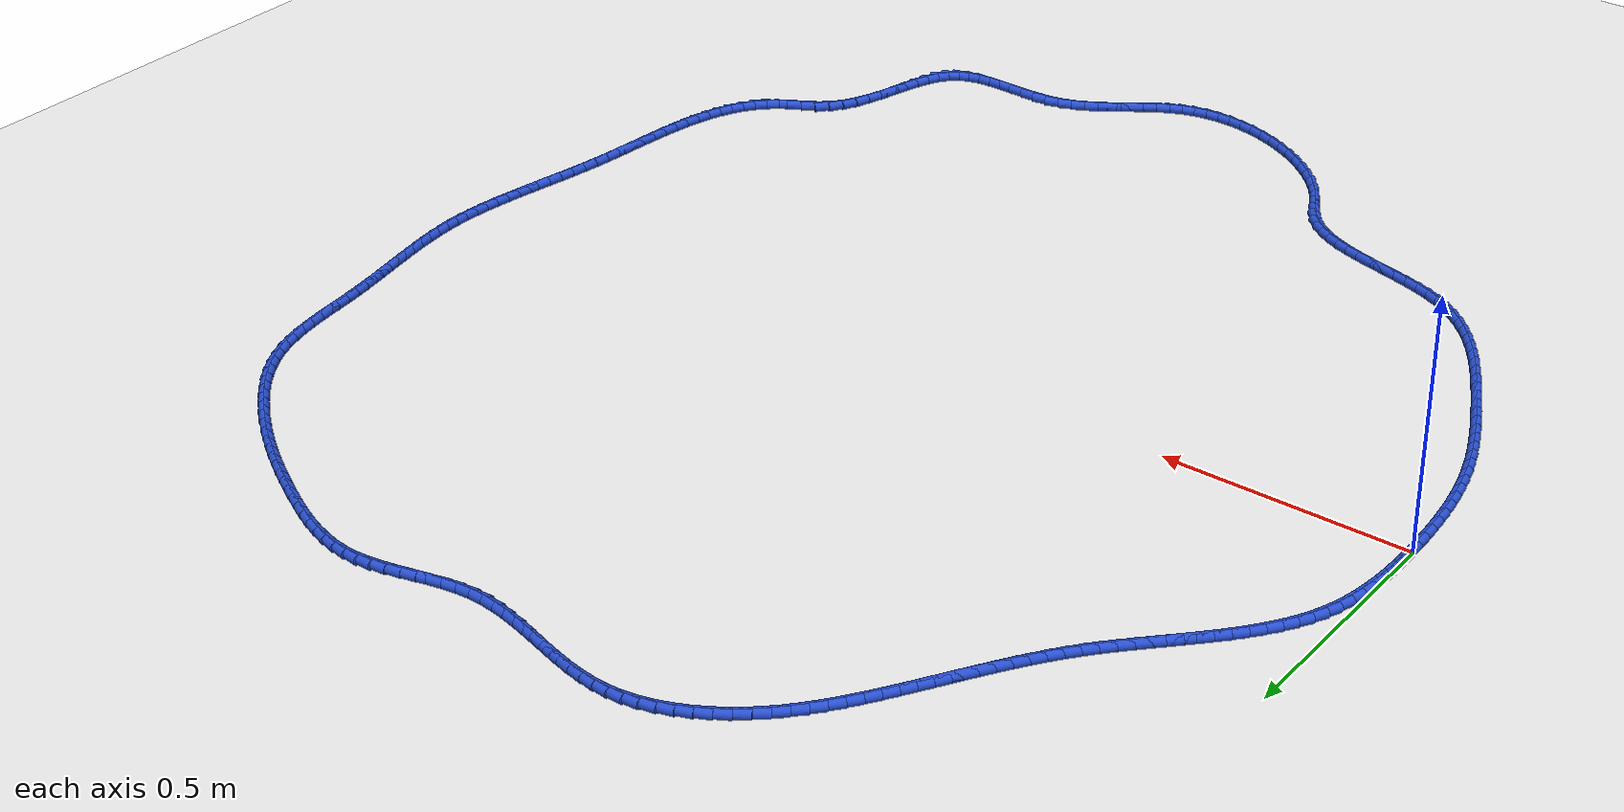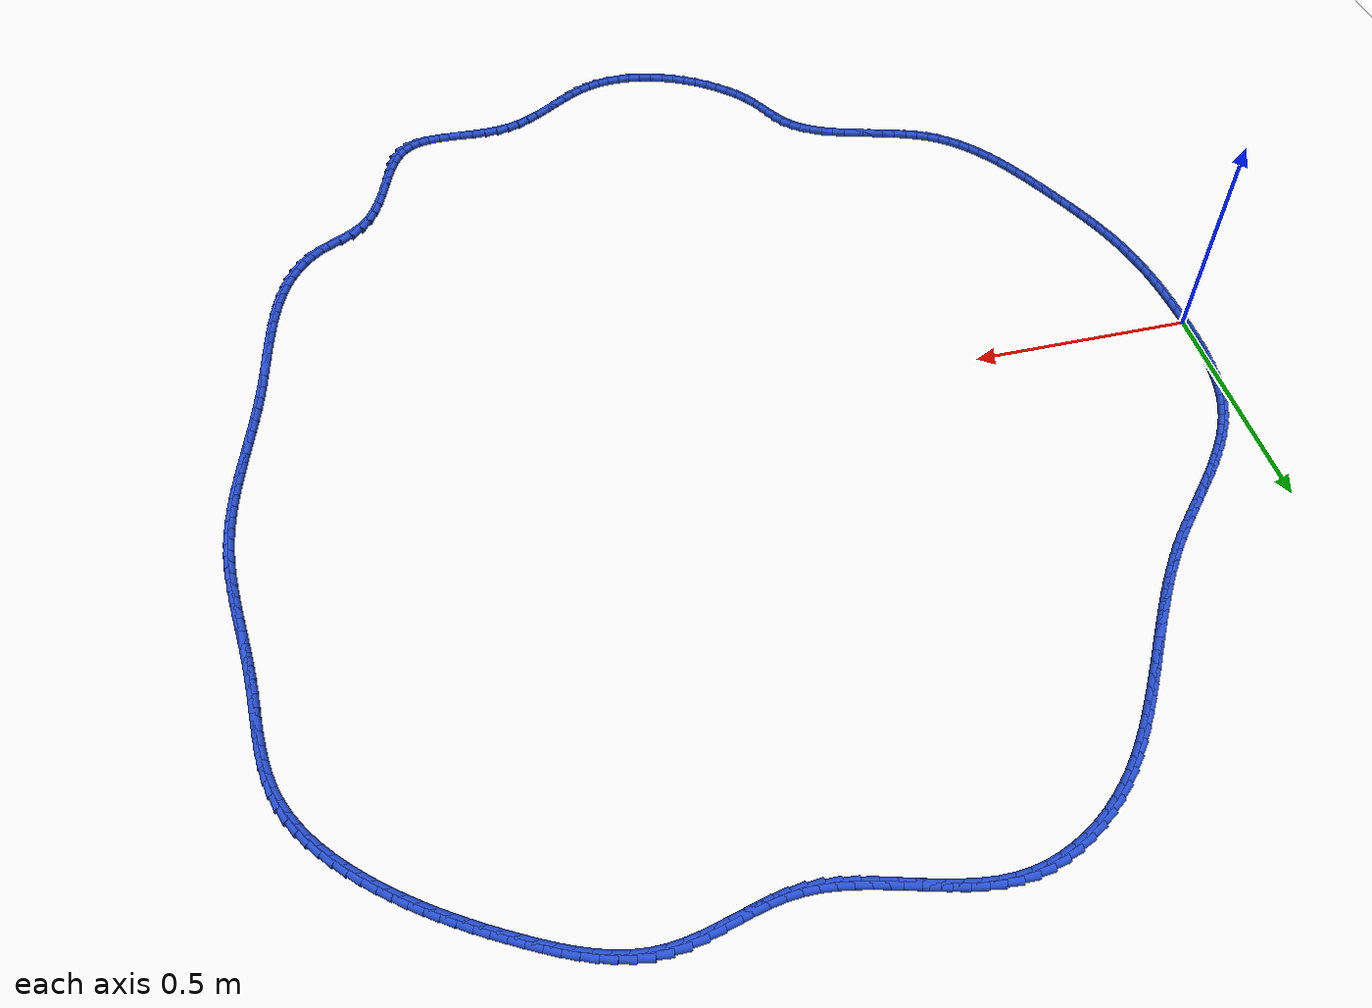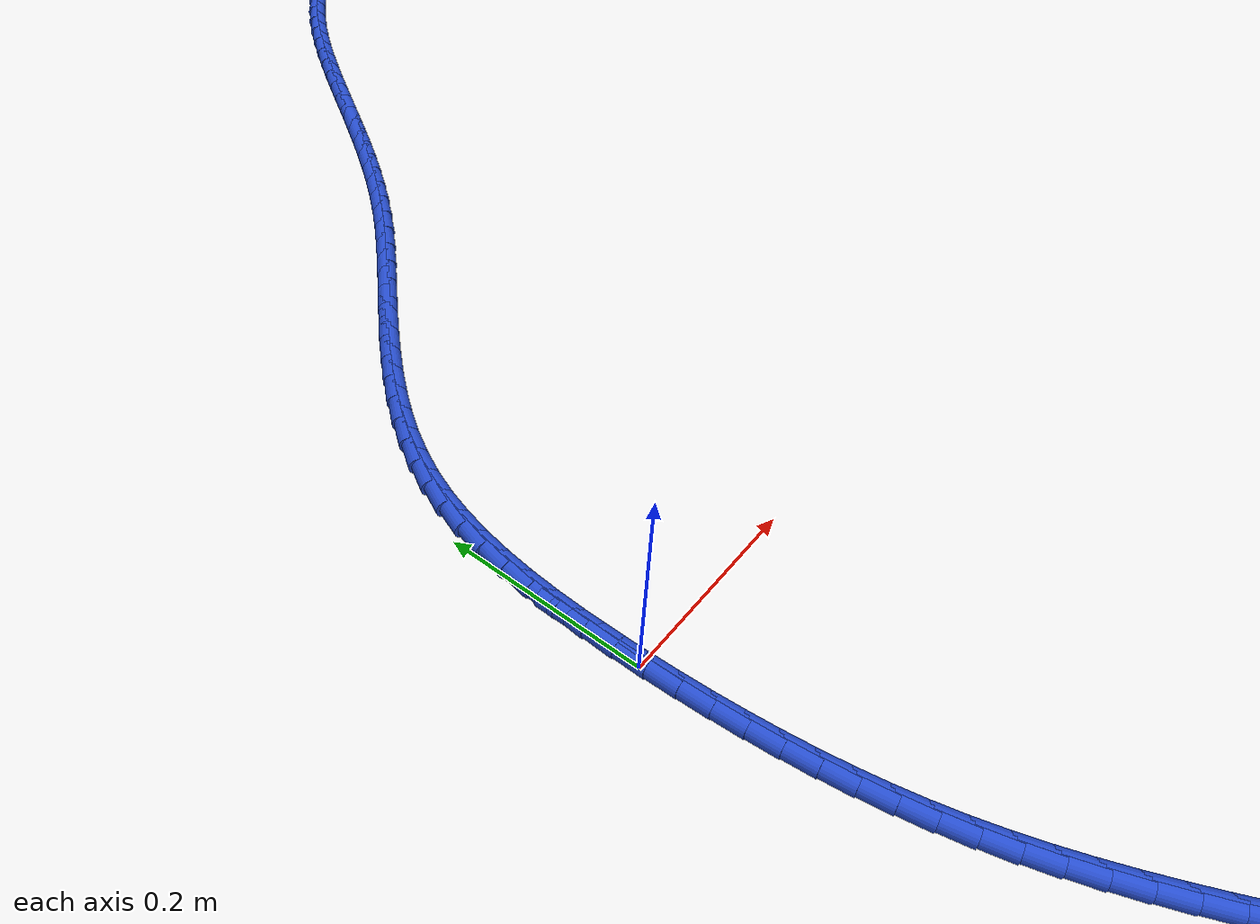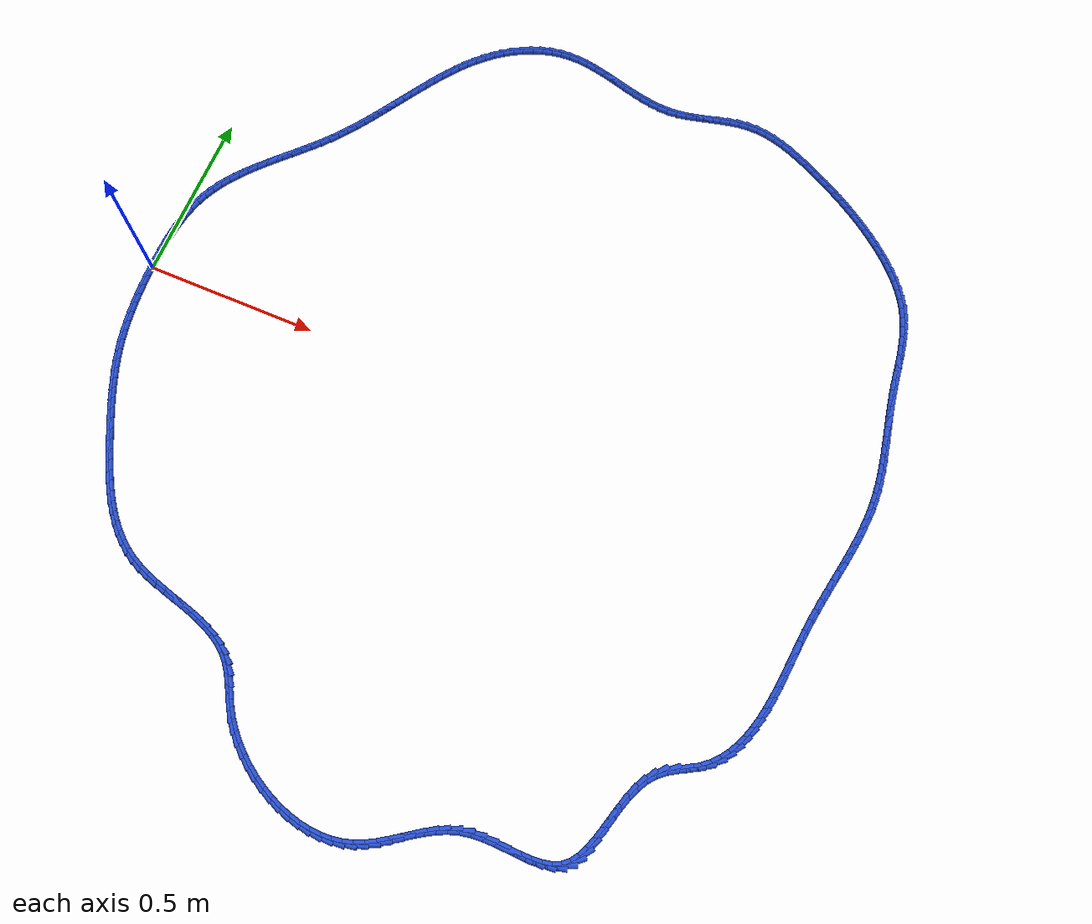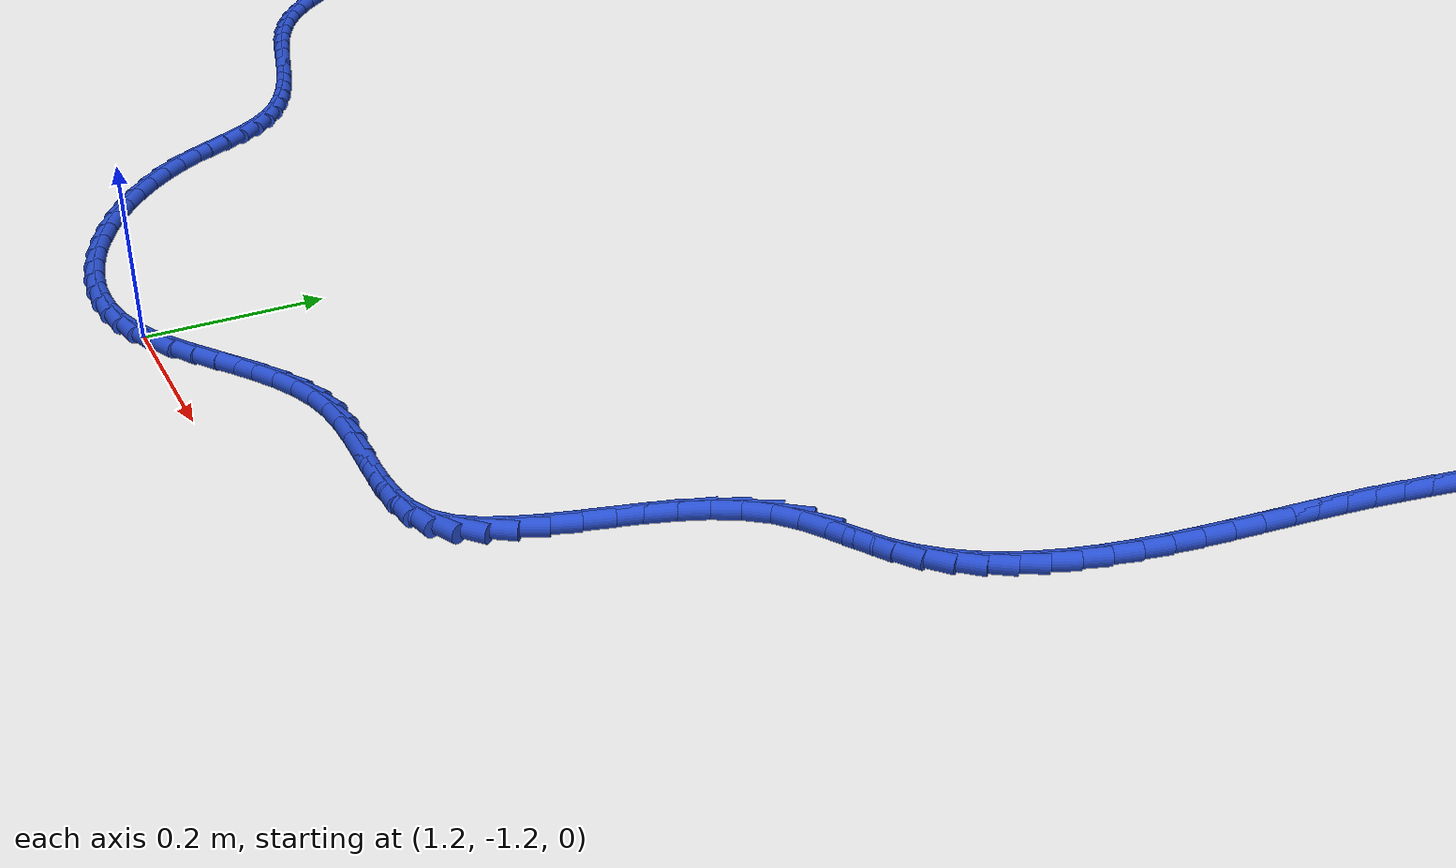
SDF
<sdf version="1.6">
 <world name="default">
  <light name="sun" type="directional">
   <pose>0 0 10 0 -0 0</pose>
   <diffuse>0.8 0.8 0.8 1</diffuse>
   <specular>0.2 0.2 0.2 1</specular>
   <attenuation>
    <range>1000</range>
    <constant>0.9</constant>
    <linear>0.01</linear>
    <quadratic>0.001</quadratic>
   </attenuation>
   <direction>-0.5 0.1 -0.9</direction>
  </light>
  <model name="ground_plane">
   <static>1</static>
   <link name="link">
    <collision name="collision">
     <geometry><plane><normal>0 0 1</normal><size>100 100</size></plane></geometry>
     <surface><friction><ode><mu>100</mu><mu2>50</mu2></ode></friction></surface>
    </collision>
    <visual name="visual">
     <cast_shadows>0</cast_shadows>
     <geometry><plane><normal>0 0 1</normal><size>100 100</size></plane></geometry>
     <material>
      <script><uri>file://media/materials/scripts/gazebo.material</uri><name>Gazebo/WhiteGlow</name></script>
     </material>
    </visual>
   </link>
  </model>
  <gravity>0 0 -9.8</gravity>
  <magnetic_field>6e-06 2.3e-05 -4.2e-05</magnetic_field>
  <atmosphere type="adiabatic"/>
  <physics name="default_physics" default="0" type="ode">
   <max_step_size>0.001</max_step_size>
   <real_time_factor>1</real_time_factor>
   <real_time_update_rate>1000</real_time_update_rate>
  </physics>
  <scene><ambient>0.4 0.4 0.4 1</ambient><background>0.7 0.7 0.7 1</background><shadows>1</shadows></scene>
  <spherical_coordinates>
   <surface_model>EARTH_WGS84</surface_model>
   <latitude_deg>0</latitude_deg>
   <longitude_deg>0</longitude_deg>
   <elevation>0</elevation>
   <heading_deg>0</heading_deg>
  </spherical_coordinates>
  <model name="line">
   <link name="link_0">
    <pose>-2.8189256484623115e-18 2.7755575615628914e-17 0.01 0 1.57 -1.5541181169794733</pose>
    <collision name="collision">
     <geometry><cylinder><radius>0.01</radius><length>0.08</length></cylinder></geometry>
    </collision>
    <visual name="visual">
     <material>
      <script><name>Gazebo/Blue</name><uri>file://media/materials/scripts/gazebo.material</uri></script>
     </material>
     <geometry><cylinder><radius>0.01</radius><length>0.08</length></cylinder></geometry>
    </visual>
   </link>
   <link name="link_1">
    <pose>-0.0005021162119911417 0.030103330034815374 0.01 0 1.57 1.564958978951634</pose>
    <collision name="collision">
     <geometry><cylinder><radius>0.01</radius><length>0.08</length></cylinder></geometry>
    </collision>
    <visual name="visual">
     <material>
      <script><name>Gazebo/Blue</name><uri>file://media/materials/scripts/gazebo.material</uri></script>
     </material>
     <geometry><cylinder><radius>0.01</radius><length>0.08</length></cylinder></geometry>
    </visual>
   </link>
   <link name="link_2">
    <pose>-0.00032616243882828286 0.060245747338506496 0.01 0 1.57 1.5363862531246002</pose>
    <collision name="collision">
     <geometry><cylinder><radius>0.01</radius><length>0.08</length></cylinder></geometry>
    </collision>
    <visual name="visual">
     <material>
      <script><name>Gazebo/Blue</name><uri>file://media/materials/scripts/gazebo.material</uri></script>
     </material>
     <geometry><cylinder><radius>0.01</radius><length>0.08</length></cylinder></geometry>
    </visual>
   </link>
   <link name="link_3">
    <pose>0.000708208300872202 0.09029399621450303 0.01 0 1.57 1.5013883025542831</pose>
    <collision name="collision">
     <geometry><cylinder><radius>0.01</radius><length>0.08</length></cylinder></geometry>
    </collision>
    <visual name="visual">
     <material>
      <script><name>Gazebo/Blue</name><uri>file://media/materials/scripts/gazebo.material</uri></script>
     </material>
     <geometry><cylinder><radius>0.01</radius><length>0.08</length></cylinder></geometry>
    </visual>
   </link>
   <link name="link_4">
    <pose>0.0027813429884939473 0.12011482096623464 0.01 0 1.57 1.4595055573976408</pose>
    <collision name="collision">
     <geometry><cylinder><radius>0.01</radius><length>0.08</length></cylinder></geometry>
    </collision>
    <visual name="visual">
     <material>
      <script><name>Gazebo/Blue</name><uri>file://media/materials/scripts/gazebo.material</uri></script>
     </material>
     <geometry><cylinder><radius>0.01</radius><length>0.08</length></cylinder></geometry>
    </visual>
   </link>
   <link name="link_5">
    <pose>0.006073588605420581 0.1495749658971309 0.01 0 1.57 1.4102192630146893</pose>
    <collision name="collision">
     <geometry><cylinder><radius>0.01</radius><length>0.08</length></cylinder></geometry>
    </collision>
    <visual name="visual">
     <material>
      <script><name>Gazebo/Blue</name><uri>file://media/materials/scripts/gazebo.material</uri></script>
     </material>
     <geometry><cylinder><radius>0.01</radius><length>0.08</length></cylinder></geometry>
    </visual>
   </link>
   <link name="link_6">
    <pose>0.01076529213303574 0.1785411753106215 0.01 0 1.57 1.3530035605198134</pose>
    <collision name="collision">
     <geometry><cylinder><radius>0.01</radius><length>0.08</length></cylinder></geometry>
    </collision>
    <visual name="visual">
     <material>
      <script><name>Gazebo/Blue</name><uri>file://media/materials/scripts/gazebo.material</uri></script>
     </material>
     <geometry><cylinder><radius>0.01</radius><length>0.08</length></cylinder></geometry>
    </visual>
   </link>
   <link name="link_7">
    <pose>0.01703680055272305 0.20688019351013612 0.01 0 1.57 1.2874062685664498</pose>
    <collision name="collision">
     <geometry><cylinder><radius>0.01</radius><length>0.08</length></cylinder></geometry>
    </collision>
    <visual name="visual">
     <material>
      <script><name>Gazebo/Blue</name><uri>file://media/materials/scripts/gazebo.material</uri></script>
     </material>
     <geometry><cylinder><radius>0.01</radius><length>0.08</length></cylinder></geometry>
    </visual>
   </link>
   <link name="link_8">
    <pose>0.025068460845866135 0.23445876479910427 0.01 0 1.57 1.2131669501022595</pose>
    <collision name="collision">
     <geometry><cylinder><radius>0.01</radius><length>0.08</length></cylinder></geometry>
    </collision>
    <visual name="visual">
     <material>
      <script><name>Gazebo/Blue</name><uri>file://media/materials/scripts/gazebo.material</uri></script>
     </material>
     <geometry><cylinder><radius>0.01</radius><length>0.08</length></cylinder></geometry>
    </visual>
   </link>
   <link name="link_9">
    <pose>0.03504057391919863 0.26114366161376984 0.01 0 1.57 1.133864592434289</pose>
    <collision name="collision">
     <geometry><cylinder><radius>0.01</radius><length>0.08</length></cylinder></geometry>
    </collision>
    <visual name="visual">
     <material>
      <script><name>Gazebo/Blue</name><uri>file://media/materials/scripts/gazebo.material</uri></script>
     </material>
     <geometry><cylinder><radius>0.01</radius><length>0.08</length></cylinder></geometry>
    </visual>
   </link>
   <link name="link_10">
    <pose>0.04704814620303539 0.2868537365181433 0.01 0 1.57 1.0609197359659526</pose>
    <collision name="collision">
     <geometry><cylinder><radius>0.01</radius><length>0.08</length></cylinder></geometry>
    </collision>
    <visual name="visual">
     <material>
      <script><name>Gazebo/Blue</name><uri>file://media/materials/scripts/gazebo.material</uri></script>
     </material>
     <geometry><cylinder><radius>0.01</radius><length>0.08</length></cylinder></geometry>
    </visual>
   </link>
   <link name="link_11">
    <pose>0.06092412018689322 0.31166785623064164 0.01 0 1.57 0.9970830469053988</pose>
    <collision name="collision">
     <geometry><cylinder><radius>0.01</radius><length>0.08</length></cylinder></geometry>
    </collision>
    <visual name="visual">
     <material>
      <script><name>Gazebo/Blue</name><uri>file://media/materials/scripts/gazebo.material</uri></script>
     </material>
     <geometry><cylinder><radius>0.01</radius><length>0.08</length></cylinder></geometry>
    </visual>
   </link>
   <link name="link_12">
    <pose>0.07645127364627094 0.3356955176444032 0.01 0 1.57 0.9425945742052655</pose>
    <collision name="collision">
     <geometry><cylinder><radius>0.01</radius><length>0.08</length></cylinder></geometry>
    </collision>
    <visual name="visual">
     <material>
      <script><name>Gazebo/Blue</name><uri>file://media/materials/scripts/gazebo.material</uri></script>
     </material>
     <geometry><cylinder><radius>0.01</radius><length>0.08</length></cylinder></geometry>
    </visual>
   </link>
   <link name="link_13">
    <pose>0.09341238435666738 0.35904621765256617 0.01 0 1.57 0.8973612643628711</pose>
    <collision name="collision">
     <geometry><cylinder><radius>0.01</radius><length>0.08</length></cylinder></geometry>
    </collision>
    <visual name="visual">
     <material>
      <script><name>Gazebo/Blue</name><uri>file://media/materials/scripts/gazebo.material</uri></script>
     </material>
     <geometry><cylinder><radius>0.01</radius><length>0.08</length></cylinder></geometry>
    </visual>
   </link>
   <link name="link_14">
    <pose>0.11159023009358124 0.38182945314826827 0.01 0 1.57 0.8611016485813237</pose>
    <collision name="collision">
     <geometry><cylinder><radius>0.01</radius><length>0.08</length></cylinder></geometry>
    </collision>
    <visual name="visual">
     <material>
      <script><name>Gazebo/Blue</name><uri>file://media/materials/scripts/gazebo.material</uri></script>
     </material>
     <geometry><cylinder><radius>0.01</radius><length>0.08</length></cylinder></geometry>
    </visual>
   </link>
   <link name="link_15">
    <pose>0.13076758863251134 0.4041547210246477 0.01 0 1.57 0.8334612381252643</pose>
    <collision name="collision">
     <geometry><cylinder><radius>0.01</radius><length>0.08</length></cylinder></geometry>
    </collision>
    <visual name="visual">
     <material>
      <script><name>Gazebo/Blue</name><uri>file://media/materials/scripts/gazebo.material</uri></script>
     </material>
     <geometry><cylinder><radius>0.01</radius><length>0.08</length></cylinder></geometry>
    </visual>
   </link>
   <link name="link_16">
    <pose>0.15072723774895652 0.42613151817484274 0.01 0 1.57 0.8140943284045029</pose>
    <collision name="collision">
     <geometry><cylinder><radius>0.01</radius><length>0.08</length></cylinder></geometry>
    </collision>
    <visual name="visual">
     <material>
      <script><name>Gazebo/Blue</name><uri>file://media/materials/scripts/gazebo.material</uri></script>
     </material>
     <geometry><cylinder><radius>0.01</radius><length>0.08</length></cylinder></geometry>
    </visual>
   </link>
   <link name="link_17">
    <pose>0.1712519552184155 0.4478693414919913 0.01 0 1.57 0.8027167475872313</pose>
    <collision name="collision">
     <geometry><cylinder><radius>0.01</radius><length>0.08</length></cylinder></geometry>
    </collision>
    <visual name="visual">
     <material>
      <script><name>Gazebo/Blue</name><uri>file://media/materials/scripts/gazebo.material</uri></script>
     </material>
     <geometry><cylinder><radius>0.01</radius><length>0.08</length></cylinder></geometry>
    </visual>
   </link>
   <link name="link_18">
    <pose>0.19212451881638715 0.46947768786923155 0.01 0 1.57 0.7991366152460926</pose>
    <collision name="collision">
     <geometry><cylinder><radius>0.01</radius><length>0.08</length></cylinder></geometry>
    </collision>
    <visual name="visual">
     <material>
      <script><name>Gazebo/Blue</name><uri>file://media/materials/scripts/gazebo.material</uri></script>
     </material>
     <geometry><cylinder><radius>0.01</radius><length>0.08</length></cylinder></geometry>
    </visual>
   </link>
   <link name="link_19">
    <pose>0.2131277063183702 0.4910660541997015 0.01 0 1.57 0.8032693308157284</pose>
    <collision name="collision">
     <geometry><cylinder><radius>0.01</radius><length>0.08</length></cylinder></geometry>
    </collision>
    <visual name="visual">
     <material>
      <script><name>Gazebo/Blue</name><uri>file://media/materials/scripts/gazebo.material</uri></script>
     </material>
     <geometry><cylinder><radius>0.01</radius><length>0.08</length></cylinder></geometry>
    </visual>
   </link>
   <link name="link_20">
    <pose>0.2340442954998635 0.5127439373765393 0.01 0 1.57 0.8151408192019713</pose>
    <collision name="collision">
     <geometry><cylinder><radius>0.01</radius><length>0.08</length></cylinder></geometry>
    </collision>
    <visual name="visual">
     <material>
      <script><name>Gazebo/Blue</name><uri>file://media/materials/scripts/gazebo.material</uri></script>
     </material>
     <geometry><cylinder><radius>0.01</radius><length>0.08</length></cylinder></geometry>
    </visual>
   </link>
   <link name="link_21">
    <pose>0.25465706413636585 0.5346208342928832 0.01 0 1.57 0.8348805298103994</pose>
    <collision name="collision">
     <geometry><cylinder><radius>0.01</radius><length>0.08</length></cylinder></geometry>
    </collision>
    <visual name="visual">
     <material>
      <script><name>Gazebo/Blue</name><uri>file://media/materials/scripts/gazebo.material</uri></script>
     </material>
     <geometry><cylinder><radius>0.01</radius><length>0.08</length></cylinder></geometry>
    </visual>
   </link>
   <link name="link_22">
    <pose>0.27474879000337593 0.5568062418418709 0.01 0 1.57 0.8626891926662084</pose>
    <collision name="collision">
     <geometry><cylinder><radius>0.01</radius><length>0.08</length></cylinder></geometry>
    </collision>
    <visual name="visual">
     <material>
      <script><name>Gazebo/Blue</name><uri>file://media/materials/scripts/gazebo.material</uri></script>
     </material>
     <geometry><cylinder><radius>0.01</radius><length>0.08</length></cylinder></geometry>
    </visual>
   </link>
   <link name="link_23">
    <pose>0.2941026314504822 0.5794094607349466 0.01 0 1.57 0.895433937974692</pose>
    <collision name="collision">
     <geometry><cylinder><radius>0.01</radius><length>0.08</length></cylinder></geometry>
    </collision>
    <visual name="visual">
     <material>
      <script><name>Gazebo/Blue</name><uri>file://media/materials/scripts/gazebo.material</uri></script>
     </material>
     <geometry><cylinder><radius>0.01</radius><length>0.08</length></cylinder></geometry>
    </visual>
   </link>
   <link name="link_24">
    <pose>0.3125928597046764 0.6024928240125467 0.01 0 1.57 0.9253701962714425</pose>
    <collision name="collision">
     <geometry><cylinder><radius>0.01</radius><length>0.08</length></cylinder></geometry>
    </collision>
    <visual name="visual">
     <material>
      <script><name>Gazebo/Blue</name><uri>file://media/materials/scripts/gazebo.material</uri></script>
     </material>
     <geometry><cylinder><radius>0.01</radius><length>0.08</length></cylinder></geometry>
    </visual>
   </link>
   <link name="link_25">
    <pose>0.33030240927161986 0.6260111011247189 0.01 0 1.57 0.951254259695157</pose>
    <collision name="collision">
     <geometry><cylinder><radius>0.01</radius><length>0.08</length></cylinder></geometry>
    </collision>
    <visual name="visual">
     <material>
      <script><name>Gazebo/Blue</name><uri>file://media/materials/scripts/gazebo.material</uri></script>
     </material>
     <geometry><cylinder><radius>0.01</radius><length>0.08</length></cylinder></geometry>
    </visual>
   </link>
   <link name="link_26">
    <pose>0.34734330098291955 0.6499040678452412 0.01 0 1.57 0.9729645868460641</pose>
    <collision name="collision">
     <geometry><cylinder><radius>0.01</radius><length>0.08</length></cylinder></geometry>
    </collision>
    <visual name="visual">
     <material>
      <script><name>Gazebo/Blue</name><uri>file://media/materials/scripts/gazebo.material</uri></script>
     </material>
     <geometry><cylinder><radius>0.01</radius><length>0.08</length></cylinder></geometry>
    </visual>
   </link>
   <link name="link_27">
    <pose>0.36382755567018255 0.6741114999478918 0.01 0 1.57 0.99042109532947</pose>
    <collision name="collision">
     <geometry><cylinder><radius>0.01</radius><length>0.08</length></cylinder></geometry>
    </collision>
    <visual name="visual">
     <material>
      <script><name>Gazebo/Blue</name><uri>file://media/materials/scripts/gazebo.material</uri></script>
     </material>
     <geometry><cylinder><radius>0.01</radius><length>0.08</length></cylinder></geometry>
    </visual>
   </link>
   <link name="link_28">
    <pose>0.37986719416501574 0.6985731732064483 0.01 0 1.57 1.0035748167725294</pose>
    <collision name="collision">
     <geometry><cylinder><radius>0.01</radius><length>0.08</length></cylinder></geometry>
    </collision>
    <visual name="visual">
     <material>
      <script><name>Gazebo/Blue</name><uri>file://media/materials/scripts/gazebo.material</uri></script>
     </material>
     <geometry><cylinder><radius>0.01</radius><length>0.08</length></cylinder></geometry>
    </visual>
   </link>
   <link name="link_29">
    <pose>0.3955742372990261 0.7232288633946887 0.01 0 1.57 1.012398882644535</pose>
    <collision name="collision">
     <geometry><cylinder><radius>0.01</radius><length>0.08</length></cylinder></geometry>
    </collision>
    <visual name="visual">
     <material>
      <script><name>Gazebo/Blue</name><uri>file://media/materials/scripts/gazebo.material</uri></script>
     </material>
     <geometry><cylinder><radius>0.01</radius><length>0.08</length></cylinder></geometry>
    </visual>
   </link>
   <link name="link_30">
    <pose>0.4110607059038206 0.7480183462863912 0.01 0 1.57 1.0168814070701326</pose>
    <collision name="collision">
     <geometry><cylinder><radius>0.01</radius><length>0.08</length></cylinder></geometry>
    </collision>
    <visual name="visual">
     <material>
      <script><name>Gazebo/Blue</name><uri>file://media/materials/scripts/gazebo.material</uri></script>
     </material>
     <geometry><cylinder><radius>0.01</radius><length>0.08</length></cylinder></geometry>
    </visual>
   </link>
   <link name="link_31">
    <pose>0.42643862081100586 0.7728813976553329 0.01 0 1.57 1.017020586156933</pose>
    <collision name="collision">
     <geometry><cylinder><radius>0.01</radius><length>0.08</length></cylinder></geometry>
    </collision>
    <visual name="visual">
     <material>
      <script><name>Gazebo/Blue</name><uri>file://media/materials/scripts/gazebo.material</uri></script>
     </material>
     <geometry><cylinder><radius>0.01</radius><length>0.08</length></cylinder></geometry>
    </visual>
   </link>
   <link name="link_32">
    <pose>0.44182000285218936 0.7977577932752928 0.01 0 1.57 1.0128221666371764</pose>
    <collision name="collision">
     <geometry><cylinder><radius>0.01</radius><length>0.08</length></cylinder></geometry>
    </collision>
    <visual name="visual">
     <material>
      <script><name>Gazebo/Blue</name><uri>file://media/materials/scripts/gazebo.material</uri></script>
     </material>
     <geometry><cylinder><radius>0.01</radius><length>0.08</length></cylinder></geometry>
    </visual>
   </link>
   <link name="link_33">
    <pose>0.4573168728589777 0.8225873089200484 0.01 0 1.57 1.0042993324878537</pose>
    <collision name="collision">
     <geometry><cylinder><radius>0.01</radius><length>0.08</length></cylinder></geometry>
    </collision>
    <visual name="visual">
     <material>
      <script><name>Gazebo/Blue</name><uri>file://media/materials/scripts/gazebo.material</uri></script>
     </material>
     <geometry><cylinder><radius>0.01</radius><length>0.08</length></cylinder></geometry>
    </visual>
   </link>
   <link name="link_34">
    <pose>0.47304125166297784 0.847309720363377 0.01 0 1.57 0.99146768256598</pose>
    <collision name="collision">
     <geometry><cylinder><radius>0.01</radius><length>0.08</length></cylinder></geometry>
    </collision>
    <visual name="visual">
     <material>
      <script><name>Gazebo/Blue</name><uri>file://media/materials/scripts/gazebo.material</uri></script>
     </material>
     <geometry><cylinder><radius>0.01</radius><length>0.08</length></cylinder></geometry>
    </visual>
   </link>
   <link name="link_35">
    <pose>0.4891052448480158 0.8718645413489473 0.01 0 1.57 0.9734752646828276</pose>
    <collision name="collision">
     <geometry><cylinder><radius>0.01</radius><length>0.08</length></cylinder></geometry>
    </collision>
    <visual name="visual">
     <material>
      <script><name>Gazebo/Blue</name><uri>file://media/materials/scripts/gazebo.material</uri></script>
     </material>
     <geometry><cylinder><radius>0.01</radius><length>0.08</length></cylinder></geometry>
    </visual>
   </link>
   <link name="link_36">
    <pose>0.5056311450640617 0.8961597900667133 0.01 0 1.57 0.9485860358934609</pose>
    <collision name="collision">
     <geometry><cylinder><radius>0.01</radius><length>0.08</length></cylinder></geometry>
    </collision>
    <visual name="visual">
     <material>
      <script><name>Gazebo/Blue</name><uri>file://media/materials/scripts/gazebo.material</uri></script>
     </material>
     <geometry><cylinder><radius>0.01</radius><length>0.08</length></cylinder></geometry>
    </visual>
   </link>
   <link name="link_37">
    <pose>0.5227609933156064 0.9200424283286979 0.01 0 1.57 0.9165215642107967</pose>
    <collision name="collision">
     <geometry><cylinder><radius>0.01</radius><length>0.08</length></cylinder></geometry>
    </collision>
    <visual name="visual">
     <material>
      <script><name>Gazebo/Blue</name><uri>file://media/materials/scripts/gazebo.material</uri></script>
     </material>
     <geometry><cylinder><radius>0.01</radius><length>0.08</length></cylinder></geometry>
    </visual>
   </link>
   <link name="link_38">
    <pose>0.5406390944891573 0.9433524186581534 0.01 0 1.57 0.8772030614403291</pose>
    <collision name="collision">
     <geometry><cylinder><radius>0.01</radius><length>0.08</length></cylinder></geometry>
    </collision>
    <visual name="visual">
     <material>
      <script><name>Gazebo/Blue</name><uri>file://media/materials/scripts/gazebo.material</uri></script>
     </material>
     <geometry><cylinder><radius>0.01</radius><length>0.08</length></cylinder></geometry>
    </visual>
   </link>
   <link name="link_39">
    <pose>0.5594097534712219 0.9659297235783328 0.01 0 1.57 0.8306063174951915</pose>
    <collision name="collision">
     <geometry><cylinder><radius>0.01</radius><length>0.08</length></cylinder></geometry>
    </collision>
    <visual name="visual">
     <material>
      <script><name>Gazebo/Blue</name><uri>file://media/materials/scripts/gazebo.material</uri></script>
     </material>
     <geometry><cylinder><radius>0.01</radius><length>0.08</length></cylinder></geometry>
    </visual>
   </link>
   <link name="link_40">
    <pose>0.5792172751483076 0.9876143056124888 0.01 0 1.57 0.7768240533221795</pose>
    <collision name="collision">
     <geometry><cylinder><radius>0.01</radius><length>0.08</length></cylinder></geometry>
    </collision>
    <visual name="visual">
     <material>
      <script><name>Gazebo/Blue</name><uri>file://media/materials/scripts/gazebo.material</uri></script>
     </material>
     <geometry><cylinder><radius>0.01</radius><length>0.08</length></cylinder></geometry>
    </visual>
   </link>
   <link name="link_41">
    <pose>0.600205964406922 1.008246127283874 0.01 0 1.57 0.7161365700888618</pose>
    <collision name="collision">
     <geometry><cylinder><radius>0.01</radius><length>0.08</length></cylinder></geometry>
    </collision>
    <visual name="visual">
     <material>
      <script><name>Gazebo/Blue</name><uri>file://media/materials/scripts/gazebo.material</uri></script>
     </material>
     <geometry><cylinder><radius>0.01</radius><length>0.08</length></cylinder></geometry>
    </visual>
   </link>
   <link name="link_42">
    <pose>0.6225201261335723 1.0276651511157413 0.01 0 1.57 0.6494190573026699</pose>
    <collision name="collision">
     <geometry><cylinder><radius>0.01</radius><length>0.08</length></cylinder></geometry>
    </collision>
    <visual name="visual">
     <material>
      <script><name>Gazebo/Blue</name><uri>file://media/materials/scripts/gazebo.material</uri></script>
     </material>
     <geometry><cylinder><radius>0.01</radius><length>0.08</length></cylinder></geometry>
    </visual>
   </link>
   <link name="link_43">
    <pose>0.6462797596173784 1.0457055587449957 0.01 0 1.57 0.5798295341526052</pose>
    <collision name="collision">
     <geometry><cylinder><radius>0.01</radius><length>0.08</length></cylinder></geometry>
    </collision>
    <visual name="visual">
     <material>
      <script><name>Gazebo/Blue</name><uri>file://media/materials/scripts/gazebo.material</uri></script>
     </material>
     <geometry><cylinder><radius>0.01</radius><length>0.08</length></cylinder></geometry>
    </visual>
   </link>
   <link name="link_44">
    <pose>0.6713889193268939 1.0621501711098023 0.01 0 1.57 0.5077270279753926</pose>
    <collision name="collision">
     <geometry><cylinder><radius>0.01</radius><length>0.08</length></cylinder></geometry>
    </collision>
    <visual name="visual">
     <material>
      <script><name>Gazebo/Blue</name><uri>file://media/materials/scripts/gazebo.material</uri></script>
     </material>
     <geometry><cylinder><radius>0.01</radius><length>0.08</length></cylinder></geometry>
    </visual>
   </link>
   <link name="link_45">
    <pose>0.6976385797558144 1.0767549140067485 0.01 0 1.57 0.4316760063939173</pose>
    <collision name="collision">
     <geometry><cylinder><radius>0.01</radius><length>0.08</length></cylinder></geometry>
    </collision>
    <visual name="visual">
     <material>
      <script><name>Gazebo/Blue</name><uri>file://media/materials/scripts/gazebo.material</uri></script>
     </material>
     <geometry><cylinder><radius>0.01</radius><length>0.08</length></cylinder></geometry>
    </visual>
   </link>
   <link name="link_46">
    <pose>0.7248187229116121 1.0892754771777406 0.01 0 1.57 0.35023896406198085</pose>
    <collision name="collision">
     <geometry><cylinder><radius>0.01</radius><length>0.08</length></cylinder></geometry>
    </collision>
    <visual name="visual">
     <material>
      <script><name>Gazebo/Blue</name><uri>file://media/materials/scripts/gazebo.material</uri></script>
     </material>
     <geometry><cylinder><radius>0.01</radius><length>0.08</length></cylinder></geometry>
    </visual>
   </link>
   <link name="link_47">
    <pose>0.7527193308017591 1.0994675503646834 0.01 0 1.57 0.2620146007174666</pose>
    <collision name="collision">
     <geometry><cylinder><radius>0.01</radius><length>0.08</length></cylinder></geometry>
    </collision>
    <visual name="visual">
     <material>
      <script><name>Gazebo/Blue</name><uri>file://media/materials/scripts/gazebo.material</uri></script>
     </material>
     <geometry><cylinder><radius>0.01</radius><length>0.08</length></cylinder></geometry>
    </visual>
   </link>
   <link name="link_48">
    <pose>0.781130385433728 1.1070868233094833 0.01 0 1.57 0.1657218443309514</pose>
    <collision name="collision">
     <geometry><cylinder><radius>0.01</radius><length>0.08</length></cylinder></geometry>
    </collision>
    <visual name="visual">
     <material>
      <script><name>Gazebo/Blue</name><uri>file://media/materials/scripts/gazebo.material</uri></script>
     </material>
     <geometry><cylinder><radius>0.01</radius><length>0.08</length></cylinder></geometry>
    </visual>
   </link>
   <link name="link_49">
    <pose>0.8098418688149909 1.1118889857540455 0.01 0 1.57 0.06192056883636127</pose>
    <collision name="collision">
     <geometry><cylinder><radius>0.01</radius><length>0.08</length></cylinder></geometry>
    </collision>
    <visual name="visual">
     <material>
      <script><name>Gazebo/Blue</name><uri>file://media/materials/scripts/gazebo.material</uri></script>
     </material>
     <geometry><cylinder><radius>0.01</radius><length>0.08</length></cylinder></geometry>
    </visual>
   </link>
   <link name="link_50">
    <pose>0.8386570171993701 1.1136755200011257 0.01 0 1.57 -0.0345685828045062</pose>
    <collision name="collision">
     <geometry><cylinder><radius>0.01</radius><length>0.08</length></cylinder></geometry>
    </collision>
    <visual name="visual">
     <material>
      <script><name>Gazebo/Blue</name><uri>file://media/materials/scripts/gazebo.material</uri></script>
     </material>
     <geometry><cylinder><radius>0.01</radius><length>0.08</length></cylinder></geometry>
    </visual>
   </link>
   <link name="link_51">
    <pose>0.8675035354584865 1.1126779393491277 0.01 0 1.57 -0.11429857854425751</pose>
    <collision name="collision">
     <geometry><cylinder><radius>0.01</radius><length>0.08</length></cylinder></geometry>
    </collision>
    <visual name="visual">
     <material>
      <script><name>Gazebo/Blue</name><uri>file://media/materials/scripts/gazebo.material</uri></script>
     </material>
     <geometry><cylinder><radius>0.01</radius><length>0.08</length></cylinder></geometry>
    </visual>
   </link>
   <link name="link_52">
    <pose>0.8963772934705438 1.1093632627698347 0.01 0 1.57 -0.17677812990244735</pose>
    <collision name="collision">
     <geometry><cylinder><radius>0.01</radius><length>0.08</length></cylinder></geometry>
    </collision>
    <visual name="visual">
     <material>
      <script><name>Gazebo/Blue</name><uri>file://media/materials/scripts/gazebo.material</uri></script>
     </material>
     <geometry><cylinder><radius>0.01</radius><length>0.08</length></cylinder></geometry>
    </visual>
   </link>
   <link name="link_53">
    <pose>0.9252748582071858 1.1042009176476189 0.01 0 1.57 -0.22243489646195638</pose>
    <collision name="collision">
     <geometry><cylinder><radius>0.01</radius><length>0.08</length></cylinder></geometry>
    </collision>
    <visual name="visual">
     <material>
      <script><name>Gazebo/Blue</name><uri>file://media/materials/scripts/gazebo.material</uri></script>
     </material>
     <geometry><cylinder><radius>0.01</radius><length>0.08</length></cylinder></geometry>
    </visual>
   </link>
   <link name="link_54">
    <pose>0.9541927966400562 1.097660331366852 0.01 0 1.57 -0.2519817851618204</pose>
    <collision name="collision">
     <geometry><cylinder><radius>0.01</radius><length>0.08</length></cylinder></geometry>
    </collision>
    <visual name="visual">
     <material>
      <script><name>Gazebo/Blue</name><uri>file://media/materials/scripts/gazebo.material</uri></script>
     </material>
     <geometry><cylinder><radius>0.01</radius><length>0.08</length></cylinder></geometry>
    </visual>
   </link>
   <link name="link_55">
    <pose>0.9831276757407983 1.0902109313119068 0.01 0 1.57 -0.26605178722382383</pose>
    <collision name="collision">
     <geometry><cylinder><radius>0.01</radius><length>0.08</length></cylinder></geometry>
    </collision>
    <visual name="visual">
     <material>
      <script><name>Gazebo/Blue</name><uri>file://media/materials/scripts/gazebo.material</uri></script>
     </material>
     <geometry><cylinder><radius>0.01</radius><length>0.08</length></cylinder></geometry>
    </visual>
   </link>
   <link name="link_56">
    <pose>1.0120760624810567 1.0823221448671554 0.01 0 1.57 -0.2649975631777457</pose>
    <collision name="collision">
     <geometry><cylinder><radius>0.01</radius><length>0.08</length></cylinder></geometry>
    </collision>
    <visual name="visual">
     <material>
      <script><name>Gazebo/Blue</name><uri>file://media/materials/scripts/gazebo.material</uri></script>
     </material>
     <geometry><cylinder><radius>0.01</radius><length>0.08</length></cylinder></geometry>
    </visual>
   </link>
   <link name="link_57">
    <pose>1.0410345238324745 1.07446339941697 0.01 0 1.57 -0.24880924447874803</pose>
    <collision name="collision">
     <geometry><cylinder><radius>0.01</radius><length>0.08</length></cylinder></geometry>
    </collision>
    <visual name="visual">
     <material>
      <script><name>Gazebo/Blue</name><uri>file://media/materials/scripts/gazebo.material</uri></script>
     </material>
     <geometry><cylinder><radius>0.01</radius><length>0.08</length></cylinder></geometry>
    </visual>
   </link>
   <link name="link_58">
    <pose>1.0699996267666956 1.0671041223457225 0.01 0 1.57 -0.2171216049999247</pose>
    <collision name="collision">
     <geometry><cylinder><radius>0.01</radius><length>0.08</length></cylinder></geometry>
    </collision>
    <visual name="visual">
     <material>
      <script><name>Gazebo/Blue</name><uri>file://media/materials/scripts/gazebo.material</uri></script>
     </material>
     <geometry><cylinder><radius>0.01</radius><length>0.08</length></cylinder></geometry>
    </visual>
   </link>
   <link name="link_59">
    <pose>1.0989679382553634 1.0607137410377852 0.01 0 1.57 -0.1693121101207636</pose>
    <collision name="collision">
     <geometry><cylinder><radius>0.01</radius><length>0.08</length></cylinder></geometry>
    </collision>
    <visual name="visual">
     <material>
      <script><name>Gazebo/Blue</name><uri>file://media/materials/scripts/gazebo.material</uri></script>
     </material>
     <geometry><cylinder><radius>0.01</radius><length>0.08</length></cylinder></geometry>
    </visual>
   </link>
   <link name="link_60">
    <pose>1.1279360252701225 1.0557616828775305 0.01 0 1.57 -0.10472055467107064</pose>
    <collision name="collision">
     <geometry><cylinder><radius>0.01</radius><length>0.08</length></cylinder></geometry>
    </collision>
    <visual name="visual">
     <material>
      <script><name>Gazebo/Blue</name><uri>file://media/materials/scripts/gazebo.material</uri></script>
     </material>
     <geometry><cylinder><radius>0.01</radius><length>0.08</length></cylinder></geometry>
    </visual>
   </link>
   <link name="link_61">
    <pose>1.1569004547826158 1.0527173752493306 0.01 0 1.57 -0.023034289158779902</pose>
    <collision name="collision">
     <geometry><cylinder><radius>0.01</radius><length>0.08</length></cylinder></geometry>
    </collision>
    <visual name="visual">
     <material>
      <script><name>Gazebo/Blue</name><uri>file://media/materials/scripts/gazebo.material</uri></script>
     </material>
     <geometry><cylinder><radius>0.01</radius><length>0.08</length></cylinder></geometry>
    </visual>
   </link>
   <link name="link_62">
    <pose>1.1858577937644874 1.0520502455375575 0.01 0 1.57 0.07282915874393478</pose>
    <collision name="collision">
     <geometry><cylinder><radius>0.01</radius><length>0.08</length></cylinder></geometry>
    </collision>
    <visual name="visual">
     <material>
      <script><name>Gazebo/Blue</name><uri>file://media/materials/scripts/gazebo.material</uri></script>
     </material>
     <geometry><cylinder><radius>0.01</radius><length>0.08</length></cylinder></geometry>
    </visual>
   </link>
   <link name="link_63">
    <pose>1.214804503902751 1.054162145305915 0.01 0 1.57 0.15611509702218304</pose>
    <collision name="collision">
     <geometry><cylinder><radius>0.01</radius><length>0.08</length></cylinder></geometry>
    </collision>
    <visual name="visual">
     <material>
      <script><name>Gazebo/Blue</name><uri>file://media/materials/scripts/gazebo.material</uri></script>
     </material>
     <geometry><cylinder><radius>0.01</radius><length>0.08</length></cylinder></geometry>
    </visual>
   </link>
   <link name="link_64">
    <pose>1.2437358953508337 1.0587158265264691 0.01 0 1.57 0.2113383226328555</pose>
    <collision name="collision">
     <geometry><cylinder><radius>0.01</radius><length>0.08</length></cylinder></geometry>
    </collision>
    <visual name="visual">
     <material>
      <script><name>Gazebo/Blue</name><uri>file://media/materials/scripts/gazebo.material</uri></script>
     </material>
     <geometry><cylinder><radius>0.01</radius><length>0.08</length></cylinder></geometry>
    </visual>
   </link>
   <link name="link_65">
    <pose>1.2726465683306345 1.0649183791652321 0.01 0 1.57 0.23945398494847578</pose>
    <collision name="collision">
     <geometry><cylinder><radius>0.01</radius><length>0.08</length></cylinder></geometry>
    </collision>
    <visual name="visual">
     <material>
      <script><name>Gazebo/Blue</name><uri>file://media/materials/scripts/gazebo.material</uri></script>
     </material>
     <geometry><cylinder><radius>0.01</radius><length>0.08</length></cylinder></geometry>
    </visual>
   </link>
   <link name="link_66">
    <pose>1.301531112629606 1.0719701959511532 0.01 0 1.57 0.24132919764163444</pose>
    <collision name="collision">
     <geometry><cylinder><radius>0.01</radius><length>0.08</length></cylinder></geometry>
    </collision>
    <visual name="visual">
     <material>
      <script><name>Gazebo/Blue</name><uri>file://media/materials/scripts/gazebo.material</uri></script>
     </material>
     <geometry><cylinder><radius>0.01</radius><length>0.08</length></cylinder></geometry>
    </visual>
   </link>
   <link name="link_67">
    <pose>1.3303841180352018 1.0790716696131821 0.01 0 1.57 0.21694717801702884</pose>
    <collision name="collision">
     <geometry><cylinder><radius>0.01</radius><length>0.08</length></cylinder></geometry>
    </collision>
    <visual name="visual">
     <material>
      <script><name>Gazebo/Blue</name><uri>file://media/materials/scripts/gazebo.material</uri></script>
     </material>
     <geometry><cylinder><radius>0.01</radius><length>0.08</length></cylinder></geometry>
    </visual>
   </link>
   <link name="link_68">
    <pose>1.359200174334876 1.0854231928802693 0.01 0 1.57 0.16536337384341823</pose>
    <collision name="collision">
     <geometry><cylinder><radius>0.01</radius><length>0.08</length></cylinder></geometry>
    </collision>
    <visual name="visual">
     <material>
      <script><name>Gazebo/Blue</name><uri>file://media/materials/scripts/gazebo.material</uri></script>
     </material>
     <geometry><cylinder><radius>0.01</radius><length>0.08</length></cylinder></geometry>
    </visual>
   </link>
   <link name="link_69">
    <pose>1.3879738713160819 1.0902251584813638 0.01 0 1.57 0.08517969117794863</pose>
    <collision name="collision">
     <geometry><cylinder><radius>0.01</radius><length>0.08</length></cylinder></geometry>
    </collision>
    <visual name="visual">
     <material>
      <script><name>Gazebo/Blue</name><uri>file://media/materials/scripts/gazebo.material</uri></script>
     </material>
     <geometry><cylinder><radius>0.01</radius><length>0.08</length></cylinder></geometry>
    </visual>
   </link>
   <link name="link_70">
    <pose>1.416699798766274 1.0926779591454163 0.01 0 1.57 -0.021218622947271636</pose>
    <collision name="collision">
     <geometry><cylinder><radius>0.01</radius><length>0.08</length></cylinder></geometry>
    </collision>
    <visual name="visual">
     <material>
      <script><name>Gazebo/Blue</name><uri>file://media/materials/scripts/gazebo.material</uri></script>
     </material>
     <geometry><cylinder><radius>0.01</radius><length>0.08</length></cylinder></geometry>
    </visual>
   </link>
   <link name="link_71">
    <pose>1.4453690356736648 1.0920695461059589 0.01 0 1.57 -0.12692684525320397</pose>
    <collision name="collision">
     <geometry><cylinder><radius>0.01</radius><length>0.08</length></cylinder></geometry>
    </collision>
    <visual name="visual">
     <material>
      <script><name>Gazebo/Blue</name><uri>file://media/materials/scripts/gazebo.material</uri></script>
     </material>
     <geometry><cylinder><radius>0.01</radius><length>0.08</length></cylinder></geometry>
    </visual>
   </link>
   <link name="link_72">
    <pose>1.4739431801302336 1.088423117191821 0.01 0 1.57 -0.21789391723330317</pose>
    <collision name="collision">
     <geometry><cylinder><radius>0.01</radius><length>0.08</length></cylinder></geometry>
    </collision>
    <visual name="visual">
     <material>
      <script><name>Gazebo/Blue</name><uri>file://media/materials/scripts/gazebo.material</uri></script>
     </material>
     <geometry><cylinder><radius>0.01</radius><length>0.08</length></cylinder></geometry>
    </visual>
   </link>
   <link name="link_73">
    <pose>1.502369095050644 1.0821293620768846 0.01 0 1.57 -0.29406613173012375</pose>
    <collision name="collision">
     <geometry><cylinder><radius>0.01</radius><length>0.08</length></cylinder></geometry>
    </collision>
    <visual name="visual">
     <material>
      <script><name>Gazebo/Blue</name><uri>file://media/materials/scripts/gazebo.material</uri></script>
     </material>
     <geometry><cylinder><radius>0.01</radius><length>0.08</length></cylinder></geometry>
    </visual>
   </link>
   <link name="link_74">
    <pose>1.5305935342266412 1.0735816919349512 0.01 0 1.57 -0.35624595211290366</pose>
    <collision name="collision">
     <geometry><cylinder><radius>0.01</radius><length>0.08</length></cylinder></geometry>
    </collision>
    <visual name="visual">
     <material>
      <script><name>Gazebo/Blue</name><uri>file://media/materials/scripts/gazebo.material</uri></script>
     </material>
     <geometry><cylinder><radius>0.01</radius><length>0.08</length></cylinder></geometry>
    </visual>
   </link>
   <link name="link_75">
    <pose>1.558563251449966 1.063173517939823 0.01 0 1.57 -0.40550951604629987</pose>
    <collision name="collision">
     <geometry><cylinder><radius>0.01</radius><length>0.08</length></cylinder></geometry>
    </collision>
    <visual name="visual">
     <material>
      <script><name>Gazebo/Blue</name><uri>file://media/materials/scripts/gazebo.material</uri></script>
     </material>
     <geometry><cylinder><radius>0.01</radius><length>0.08</length></cylinder></geometry>
    </visual>
   </link>
   <link name="link_76">
    <pose>1.5862250005123621 1.0512982512653022 0.01 0 1.57 -0.44288615182390334</pose>
    <collision name="collision">
     <geometry><cylinder><radius>0.01</radius><length>0.08</length></cylinder></geometry>
    </collision>
    <visual name="visual">
     <material>
      <script><name>Gazebo/Blue</name><uri>file://media/materials/scripts/gazebo.material</uri></script>
     </material>
     <geometry><cylinder><radius>0.01</radius><length>0.08</length></cylinder></geometry>
    </visual>
   </link>
   <link name="link_77">
    <pose>1.6135255352055728 1.0383493030851905 0.01 0 1.57 -0.46917211299571915</pose>
    <collision name="collision">
     <geometry><cylinder><radius>0.01</radius><length>0.08</length></cylinder></geometry>
    </collision>
    <visual name="visual">
     <material>
      <script><name>Gazebo/Blue</name><uri>file://media/materials/scripts/gazebo.material</uri></script>
     </material>
     <geometry><cylinder><radius>0.01</radius><length>0.08</length></cylinder></geometry>
    </visual>
   </link>
   <link name="link_78">
    <pose>1.6404116093213408 1.0247200845732893 0.01 0 1.57 -0.48589859762808674</pose>
    <collision name="collision">
     <geometry><cylinder><radius>0.01</radius><length>0.08</length></cylinder></geometry>
    </collision>
    <visual name="visual">
     <material>
      <script><name>Gazebo/Blue</name><uri>file://media/materials/scripts/gazebo.material</uri></script>
     </material>
     <geometry><cylinder><radius>0.01</radius><length>0.08</length></cylinder></geometry>
    </visual>
   </link>
   <link name="link_79">
    <pose>1.666835811844344 1.0107646347210333 0.01 0 1.57 -0.5012498170042013</pose>
    <collision name="collision">
     <geometry><cylinder><radius>0.01</radius><length>0.08</length></cylinder></geometry>
    </collision>
    <visual name="visual">
     <material>
      <script><name>Gazebo/Blue</name><uri>file://media/materials/scripts/gazebo.material</uri></script>
     </material>
     <geometry><cylinder><radius>0.01</radius><length>0.08</length></cylinder></geometry>
    </visual>
   </link>
   <link name="link_80">
    <pose>1.6927945788015677 0.9965411404777652 0.01 0 1.57 -0.5188773775584801</pose>
    <collision name="collision">
     <geometry><cylinder><radius>0.01</radius><length>0.08</length></cylinder></geometry>
    </collision>
    <visual name="visual">
     <material>
      <script><name>Gazebo/Blue</name><uri>file://media/materials/scripts/gazebo.material</uri></script>
     </material>
     <geometry><cylinder><radius>0.01</radius><length>0.08</length></cylinder></geometry>
    </visual>
   </link>
   <link name="link_81">
    <pose>1.7183042844407013 0.9819732583205157 0.01 0 1.57 -0.5387470754433419</pose>
    <collision name="collision">
     <geometry><cylinder><radius>0.01</radius><length>0.08</length></cylinder></geometry>
    </collision>
    <visual name="visual">
     <material>
      <script><name>Gazebo/Blue</name><uri>file://media/materials/scripts/gazebo.material</uri></script>
     </material>
     <geometry><cylinder><radius>0.01</radius><length>0.08</length></cylinder></geometry>
    </visual>
   </link>
   <link name="link_82">
    <pose>1.7433814033484387 0.966983967702319 0.01 0 1.57 -0.560771373461822</pose>
    <collision name="collision">
     <geometry><cylinder><radius>0.01</radius><length>0.08</length></cylinder></geometry>
    </collision>
    <visual name="visual">
     <material>
      <script><name>Gazebo/Blue</name><uri>file://media/materials/scripts/gazebo.material</uri></script>
     </material>
     <geometry><cylinder><radius>0.01</radius><length>0.08</length></cylinder></geometry>
    </visual>
   </link>
   <link name="link_83">
    <pose>1.7680424101114747 0.9514962480762086 0.01 0 1.57 -0.5848262778411262</pose>
    <collision name="collision">
     <geometry><cylinder><radius>0.01</radius><length>0.08</length></cylinder></geometry>
    </collision>
    <visual name="visual">
     <material>
      <script><name>Gazebo/Blue</name><uri>file://media/materials/scripts/gazebo.material</uri></script>
     </material>
     <geometry><cylinder><radius>0.01</radius><length>0.08</length></cylinder></geometry>
    </visual>
   </link>
   <link name="link_84">
    <pose>1.792303779316505 0.9354330788952191 0.01 0 1.57 -0.6107511172986645</pose>
    <collision name="collision">
     <geometry><cylinder><radius>0.01</radius><length>0.08</length></cylinder></geometry>
    </collision>
    <visual name="visual">
     <material>
      <script><name>Gazebo/Blue</name><uri>file://media/materials/scripts/gazebo.material</uri></script>
     </material>
     <geometry><cylinder><radius>0.01</radius><length>0.08</length></cylinder></geometry>
    </visual>
   </link>
   <link name="link_85">
    <pose>1.816181985550224 0.9187174396123834 0.01 0 1.57 -0.6383499978164633</pose>
    <collision name="collision">
     <geometry><cylinder><radius>0.01</radius><length>0.08</length></cylinder></geometry>
    </collision>
    <visual name="visual">
     <material>
      <script><name>Gazebo/Blue</name><uri>file://media/materials/scripts/gazebo.material</uri></script>
     </material>
     <geometry><cylinder><radius>0.01</radius><length>0.08</length></cylinder></geometry>
    </visual>
   </link>
   <link name="link_86">
    <pose>1.8396935033993267 0.9012723096807367 0.01 0 1.57 -0.6673951291879331</pose>
    <collision name="collision">
     <geometry><cylinder><radius>0.01</radius><length>0.08</length></cylinder></geometry>
    </collision>
    <visual name="visual">
     <material>
      <script><name>Gazebo/Blue</name><uri>file://media/materials/scripts/gazebo.material</uri></script>
     </material>
     <geometry><cylinder><radius>0.01</radius><length>0.08</length></cylinder></geometry>
    </visual>
   </link>
   <link name="link_87">
    <pose>1.8628548074505074 0.8830206685533124 0.01 0 1.57 -0.6980067632715559</pose>
    <collision name="collision">
     <geometry><cylinder><radius>0.01</radius><length>0.08</length></cylinder></geometry>
    </collision>
    <visual name="visual">
     <material>
      <script><name>Gazebo/Blue</name><uri>file://media/materials/scripts/gazebo.material</uri></script>
     </material>
     <geometry><cylinder><radius>0.01</radius><length>0.08</length></cylinder></geometry>
    </visual>
   </link>
   <link name="link_88">
    <pose>1.885656845838557 0.8638923407009681 0.01 0 1.57 -0.7326987604007634</pose>
    <collision name="collision">
     <geometry><cylinder><radius>0.01</radius><length>0.08</length></cylinder></geometry>
    </collision>
    <visual name="visual">
     <material>
      <script><name>Gazebo/Blue</name><uri>file://media/materials/scripts/gazebo.material</uri></script>
     </material>
     <geometry><cylinder><radius>0.01</radius><length>0.08</length></cylinder></geometry>
    </visual>
   </link>
   <link name="link_89">
    <pose>1.907915726763709 0.843864034606201 0.01 0 1.57 -0.7729753488264226</pose>
    <collision name="collision">
     <geometry><cylinder><radius>0.01</radius><length>0.08</length></cylinder></geometry>
    </collision>
    <visual name="visual">
     <material>
      <script><name>Gazebo/Blue</name><uri>file://media/materials/scripts/gazebo.material</uri></script>
     </material>
     <geometry><cylinder><radius>0.01</radius><length>0.08</length></cylinder></geometry>
    </visual>
   </link>
   <link name="link_90">
    <pose>1.9293742923954078 0.8229321053239544 0.01 0 1.57 -0.8194353994487286</pose>
    <collision name="collision">
     <geometry><cylinder><radius>0.01</radius><length>0.08</length></cylinder></geometry>
    </collision>
    <visual name="visual">
     <material>
      <script><name>Gazebo/Blue</name><uri>file://media/materials/scripts/gazebo.material</uri></script>
     </material>
     <geometry><cylinder><radius>0.01</radius><length>0.08</length></cylinder></geometry>
    </visual>
   </link>
   <link name="link_91">
    <pose>1.9497751355007242 0.8010929747873913 0.01 0 1.57 -0.8727607862284106</pose>
    <collision name="collision">
     <geometry><cylinder><radius>0.01</radius><length>0.08</length></cylinder></geometry>
    </collision>
    <visual name="visual">
     <material>
      <script><name>Gazebo/Blue</name><uri>file://media/materials/scripts/gazebo.material</uri></script>
     </material>
     <geometry><cylinder><radius>0.01</radius><length>0.08</length></cylinder></geometry>
    </visual>
   </link>
   <link name="link_92">
    <pose>1.9688608488467296 0.7783430649296749 0.01 0 1.57 -0.9336818026973555</pose>
    <collision name="collision">
     <geometry><cylinder><radius>0.01</radius><length>0.08</length></cylinder></geometry>
    </collision>
    <visual name="visual">
     <material>
      <script><name>Gazebo/Blue</name><uri>file://media/materials/scripts/gazebo.material</uri></script>
     </material>
     <geometry><cylinder><radius>0.01</radius><length>0.08</length></cylinder></geometry>
    </visual>
   </link>
   <link name="link_93">
    <pose>1.9863740252004938 0.7546787976839681 0.01 0 1.57 -1.002909430333122</pose>
    <collision name="collision">
     <geometry><cylinder><radius>0.01</radius><length>0.08</length></cylinder></geometry>
    </collision>
    <visual name="visual">
     <material>
      <script><name>Gazebo/Blue</name><uri>file://media/materials/scripts/gazebo.material</uri></script>
     </material>
     <geometry><cylinder><radius>0.01</radius><length>0.08</length></cylinder></geometry>
    </visual>
   </link>
   <link name="link_94">
    <pose>2.0020572573290885 0.7300965949834349 0.01 0 1.57 -1.0810252726237681</pose>
    <collision name="collision">
     <geometry><cylinder><radius>0.01</radius><length>0.08</length></cylinder></geometry>
    </collision>
    <visual name="visual">
     <material>
      <script><name>Gazebo/Blue</name><uri>file://media/materials/scripts/gazebo.material</uri></script>
     </material>
     <geometry><cylinder><radius>0.01</radius><length>0.08</length></cylinder></geometry>
    </visual>
   </link>
   <link name="link_95">
    <pose>2.015653137999584 0.7045928787612383 0.01 0 1.57 -1.167430268676624</pose>
    <collision name="collision">
     <geometry><cylinder><radius>0.01</radius><length>0.08</length></cylinder></geometry>
    </collision>
    <visual name="visual">
     <material>
      <script><name>Gazebo/Blue</name><uri>file://media/materials/scripts/gazebo.material</uri></script>
     </material>
     <geometry><cylinder><radius>0.01</radius><length>0.08</length></cylinder></geometry>
    </visual>
   </link>
   <link name="link_96">
    <pose>2.02692984164409 0.6781692961768293 0.01 0 1.57 -1.2495726912025036</pose>
    <collision name="collision">
     <geometry><cylinder><radius>0.01</radius><length>0.08</length></cylinder></geometry>
    </collision>
    <visual name="visual">
     <material>
      <script><name>Gazebo/Blue</name><uri>file://media/materials/scripts/gazebo.material</uri></script>
     </material>
     <geometry><cylinder><radius>0.01</radius><length>0.08</length></cylinder></geometry>
    </visual>
   </link>
   <link name="link_97">
    <pose>2.036004081890568 0.6508986858529946 0.01 0 1.57 -1.3176994537244056</pose>
    <collision name="collision">
     <geometry><cylinder><radius>0.01</radius><length>0.08</length></cylinder></geometry>
    </collision>
    <visual name="visual">
     <material>
      <script><name>Gazebo/Blue</name><uri>file://media/materials/scripts/gazebo.material</uri></script>
     </material>
     <geometry><cylinder><radius>0.01</radius><length>0.08</length></cylinder></geometry>
    </visual>
   </link>
   <link name="link_98">
    <pose>2.0432443793386836 0.6229053196716963 0.01 0 1.57 -1.3713055641967067</pose>
    <collision name="collision">
     <geometry><cylinder><radius>0.01</radius><length>0.08</length></cylinder></geometry>
    </collision>
    <visual name="visual">
     <material>
      <script><name>Gazebo/Blue</name><uri>file://media/materials/scripts/gazebo.material</uri></script>
     </material>
     <geometry><cylinder><radius>0.01</radius><length>0.08</length></cylinder></geometry>
    </visual>
   </link>
   <link name="link_99">
    <pose>2.0490248466001217 0.594314611720776 0.01 0 1.57 -1.4106408211546666</pose>
    <collision name="collision">
     <geometry><cylinder><radius>0.01</radius><length>0.08</length></cylinder></geometry>
    </collision>
    <visual name="visual">
     <material>
      <script><name>Gazebo/Blue</name><uri>file://media/materials/scripts/gazebo.material</uri></script>
     </material>
     <geometry><cylinder><radius>0.01</radius><length>0.08</length></cylinder></geometry>
    </visual>
   </link>
   <link name="link_100">
    <pose>2.0537195962865673 0.5652519760880748 0.01 0 1.57 -1.436176516224542</pose>
    <collision name="collision">
     <geometry><cylinder><radius>0.01</radius><length>0.08</length></cylinder></geometry>
    </collision>
    <visual name="visual">
     <material>
      <script><name>Gazebo/Blue</name><uri>file://media/materials/scripts/gazebo.material</uri></script>
     </material>
     <geometry><cylinder><radius>0.01</radius><length>0.08</length></cylinder></geometry>
    </visual>
   </link>
   <link name="link_101">
    <pose>2.0577027410097046 0.5358428268614347 0.01 0 1.57 -1.448373418073811</pose>
    <collision name="collision">
     <geometry><cylinder><radius>0.01</radius><length>0.08</length></cylinder></geometry>
    </collision>
    <visual name="visual">
     <material>
      <script><name>Gazebo/Blue</name><uri>file://media/materials/scripts/gazebo.material</uri></script>
     </material>
     <geometry><cylinder><radius>0.01</radius><length>0.08</length></cylinder></geometry>
    </visual>
   </link>
   <link name="link_102">
    <pose>2.0613483933812193 0.5062125781286972 0.01 0 1.57 -1.4475500873538036</pose>
    <collision name="collision">
     <geometry><cylinder><radius>0.01</radius><length>0.08</length></cylinder></geometry>
    </collision>
    <visual name="visual">
     <material>
      <script><name>Gazebo/Blue</name><uri>file://media/materials/scripts/gazebo.material</uri></script>
     </material>
     <geometry><cylinder><radius>0.01</radius><length>0.08</length></cylinder></geometry>
    </visual>
   </link>
   <link name="link_103">
    <pose>2.0650306660127953 0.47648664397770385 0.01 0 1.57 -1.4338547506117405</pose>
    <collision name="collision">
     <geometry><cylinder><radius>0.01</radius><length>0.08</length></cylinder></geometry>
    </collision>
    <visual name="visual">
     <material>
      <script><name>Gazebo/Blue</name><uri>file://media/materials/scripts/gazebo.material</uri></script>
     </material>
     <geometry><cylinder><radius>0.01</radius><length>0.08</length></cylinder></geometry>
    </visual>
   </link>
   <link name="link_104">
    <pose>2.0691229460274108 0.4467902781723724 0.01 0 1.57 -1.4126595295496769</pose>
    <collision name="collision">
     <geometry><cylinder><radius>0.01</radius><length>0.08</length></cylinder></geometry>
    </collision>
    <visual name="visual">
     <material>
      <script><name>Gazebo/Blue</name><uri>file://media/materials/scripts/gazebo.material</uri></script>
     </material>
     <geometry><cylinder><radius>0.01</radius><length>0.08</length></cylinder></geometry>
    </visual>
   </link>
   <link name="link_105">
    <pose>2.0738394936798086 0.41721356943048943 0.01 0 1.57 -1.3960899454977034</pose>
    <collision name="collision">
     <geometry><cylinder><radius>0.01</radius><length>0.08</length></cylinder></geometry>
    </collision>
    <visual name="visual">
     <material>
      <script><name>Gazebo/Blue</name><uri>file://media/materials/scripts/gazebo.material</uri></script>
     </material>
     <geometry><cylinder><radius>0.01</radius><length>0.08</length></cylinder></geometry>
    </visual>
   </link>
   <link name="link_106">
    <pose>2.0790368856605475 0.38776756287918457 0.01 0 1.57 -1.385796669029892</pose>
    <collision name="collision">
     <geometry><cylinder><radius>0.01</radius><length>0.08</length></cylinder></geometry>
    </collision>
    <visual name="visual">
     <material>
      <script><name>Gazebo/Blue</name><uri>file://media/materials/scripts/gazebo.material</uri></script>
     </material>
     <geometry><cylinder><radius>0.01</radius><length>0.08</length></cylinder></geometry>
    </visual>
   </link>
   <link name="link_107">
    <pose>2.0845228882675784 0.3584525171597675 0.01 0 1.57 -1.381796054233603</pose>
    <collision name="collision">
     <geometry><cylinder><radius>0.01</radius><length>0.08</length></cylinder></geometry>
    </collision>
    <visual name="visual">
     <material>
      <script><name>Gazebo/Blue</name><uri>file://media/materials/scripts/gazebo.material</uri></script>
     </material>
     <geometry><cylinder><radius>0.01</radius><length>0.08</length></cylinder></geometry>
    </visual>
   </link>
   <link name="link_108">
    <pose>2.0901052677988528 0.32926869091354793 0.01 0 1.57 -1.384144983832363</pose>
    <collision name="collision">
     <geometry><cylinder><radius>0.01</radius><length>0.08</length></cylinder></geometry>
    </collision>
    <visual name="visual">
     <material>
      <script><name>Gazebo/Blue</name><uri>file://media/materials/scripts/gazebo.material</uri></script>
     </material>
     <geometry><cylinder><radius>0.01</radius><length>0.08</length></cylinder></geometry>
    </visual>
   </link>
   <link name="link_109">
    <pose>2.0955917905523203 0.3002163427818364 0.01 0 1.57 -1.3929471483996352</pose>
    <collision name="collision">
     <geometry><cylinder><radius>0.01</radius><length>0.08</length></cylinder></geometry>
    </collision>
    <visual name="visual">
     <material>
      <script><name>Gazebo/Blue</name><uri>file://media/materials/scripts/gazebo.material</uri></script>
     </material>
     <geometry><cylinder><radius>0.01</radius><length>0.08</length></cylinder></geometry>
    </visual>
   </link>
   <link name="link_110">
    <pose>2.100790222825933 0.27129573140594243 0.01 0 1.57 -1.4083524495396587</pose>
    <collision name="collision">
     <geometry><cylinder><radius>0.01</radius><length>0.08</length></cylinder></geometry>
    </collision>
    <visual name="visual">
     <material>
      <script><name>Gazebo/Blue</name><uri>file://media/materials/scripts/gazebo.material</uri></script>
     </material>
     <geometry><cylinder><radius>0.01</radius><length>0.08</length></cylinder></geometry>
    </visual>
   </link>
   <link name="link_111">
    <pose>2.1055083309176412 0.24250711542717593 0.01 0 1.57 -1.4305485589471085</pose>
    <collision name="collision">
     <geometry><cylinder><radius>0.01</radius><length>0.08</length></cylinder></geometry>
    </collision>
    <visual name="visual">
     <material>
      <script><name>Gazebo/Blue</name><uri>file://media/materials/scripts/gazebo.material</uri></script>
     </material>
     <geometry><cylinder><radius>0.01</radius><length>0.08</length></cylinder></geometry>
    </visual>
   </link>
   <link name="link_112">
    <pose>2.109553881125396 0.21385075348684635 0.01 0 1.57 -1.459742875718456</pose>
    <collision name="collision">
     <geometry><cylinder><radius>0.01</radius><length>0.08</length></cylinder></geometry>
    </collision>
    <visual name="visual">
     <material>
      <script><name>Gazebo/Blue</name><uri>file://media/materials/scripts/gazebo.material</uri></script>
     </material>
     <geometry><cylinder><radius>0.01</radius><length>0.08</length></cylinder></geometry>
    </visual>
   </link>
   <link name="link_113">
    <pose>2.112734639747148 0.18532690422626433 0.01 0 1.57 -1.496132536580306</pose>
    <collision name="collision">
     <geometry><cylinder><radius>0.01</radius><length>0.08</length></cylinder></geometry>
    </collision>
    <visual name="visual">
     <material>
      <script><name>Gazebo/Blue</name><uri>file://media/materials/scripts/gazebo.material</uri></script>
     </material>
     <geometry><cylinder><radius>0.01</radius><length>0.08</length></cylinder></geometry>
    </visual>
   </link>
   <link name="link_114">
    <pose>2.114858373080848 0.1569358262867394 0.01 0 1.57 -1.5396754192267976</pose>
    <collision name="collision">
     <geometry><cylinder><radius>0.01</radius><length>0.08</length></cylinder></geometry>
    </collision>
    <visual name="visual">
     <material>
      <script><name>Gazebo/Blue</name><uri>file://media/materials/scripts/gazebo.material</uri></script>
     </material>
     <geometry><cylinder><radius>0.01</radius><length>0.08</length></cylinder></geometry>
    </visual>
   </link>
   <link name="link_115">
    <pose>2.1157380988905805 0.1286769530048305 0.01 0 1.57 1.5565921139285408</pose>
    <collision name="collision">
     <geometry><cylinder><radius>0.01</radius><length>0.08</length></cylinder></geometry>
    </collision>
    <visual name="visual">
     <material>
      <script><name>Gazebo/Blue</name><uri>file://media/materials/scripts/gazebo.material</uri></script>
     </material>
     <geometry><cylinder><radius>0.01</radius><length>0.08</length></cylinder></geometry>
    </visual>
   </link>
   <link name="link_116">
    <pose>2.1153382088482355 0.10052592824534286 0.01 0 1.57 1.5158761207936855</pose>
    <collision name="collision">
     <geometry><cylinder><radius>0.01</radius><length>0.08</length></cylinder></geometry>
    </collision>
    <visual name="visual">
     <material>
      <script><name>Gazebo/Blue</name><uri>file://media/materials/scripts/gazebo.material</uri></script>
     </material>
     <geometry><cylinder><radius>0.01</radius><length>0.08</length></cylinder></geometry>
    </visual>
   </link>
   <link name="link_117">
    <pose>2.113793708436274 0.07243158271560653 0.01 0 1.57 1.4804426431278395</pose>
    <collision name="collision">
     <geometry><cylinder><radius>0.01</radius><length>0.08</length></cylinder></geometry>
    </collision>
    <visual name="visual">
     <material>
      <script><name>Gazebo/Blue</name><uri>file://media/materials/scripts/gazebo.material</uri></script>
     </material>
     <geometry><cylinder><radius>0.01</radius><length>0.08</length></cylinder></geometry>
    </visual>
   </link>
   <link name="link_118">
    <pose>2.111248719860951 0.044341314365838845 0.01 0 1.57 1.4505021827783793</pose>
    <collision name="collision">
     <geometry><cylinder><radius>0.01</radius><length>0.08</length></cylinder></geometry>
    </collision>
    <visual name="visual">
     <material>
      <script><name>Gazebo/Blue</name><uri>file://media/materials/scripts/gazebo.material</uri></script>
     </material>
     <geometry><cylinder><radius>0.01</radius><length>0.08</length></cylinder></geometry>
    </visual>
   </link>
   <link name="link_119">
    <pose>2.107847365328518 0.01620252114625676 0.01 0 1.57 1.4261476091777</pose>
    <collision name="collision">
     <geometry><cylinder><radius>0.01</radius><length>0.08</length></cylinder></geometry>
    </collision>
    <visual name="visual">
     <material>
      <script><name>Gazebo/Blue</name><uri>file://media/materials/scripts/gazebo.material</uri></script>
     </material>
     <geometry><cylinder><radius>0.01</radius><length>0.08</length></cylinder></geometry>
    </visual>
   </link>
   <link name="link_120">
    <pose>2.103733767045229 -0.012037398992921573 0.01 0 1.57 1.4073805308594722</pose>
    <collision name="collision">
     <geometry><cylinder><radius>0.01</radius><length>0.08</length></cylinder></geometry>
    </collision>
    <visual name="visual">
     <material>
      <script><name>Gazebo/Blue</name><uri>file://media/materials/scripts/gazebo.material</uri></script>
     </material>
     <geometry><cylinder><radius>0.01</radius><length>0.08</length></cylinder></geometry>
    </visual>
   </link>
   <link name="link_121">
    <pose>2.099052047217337 -0.040431048101479225 0.01 0 1.57 1.394135592030088</pose>
    <collision name="collision">
     <geometry><cylinder><radius>0.01</radius><length>0.08</length></cylinder></geometry>
    </collision>
    <visual name="visual">
     <material>
      <script><name>Gazebo/Blue</name><uri>file://media/materials/scripts/gazebo.material</uri></script>
     </material>
     <geometry><cylinder><radius>0.01</radius><length>0.08</length></cylinder></geometry>
    </visual>
   </link>
   <link name="link_122">
    <pose>2.0939463280510955 -0.06903102822919878 0.01 0 1.57 1.3863004362870255</pose>
    <collision name="collision">
     <geometry><cylinder><radius>0.01</radius><length>0.08</length></cylinder></geometry>
    </collision>
    <visual name="visual">
     <material>
      <script><name>Gazebo/Blue</name><uri>file://media/materials/scripts/gazebo.material</uri></script>
     </material>
     <geometry><cylinder><radius>0.01</radius><length>0.08</length></cylinder></geometry>
    </visual>
   </link>
   <link name="link_123">
    <pose>2.088560731752757 -0.09788994142586294 0.01 0 1.57 1.3837304192240876</pose>
    <collision name="collision">
     <geometry><cylinder><radius>0.01</radius><length>0.08</length></cylinder></geometry>
    </collision>
    <visual name="visual">
     <material>
      <script><name>Gazebo/Blue</name><uri>file://media/materials/scripts/gazebo.material</uri></script>
     </material>
     <geometry><cylinder><radius>0.01</radius><length>0.08</length></cylinder></geometry>
    </visual>
   </link>
   <link name="link_124">
    <pose>2.0830393805285743 -0.12706038974125428 0.01 0 1.57 1.3862580670129987</pose>
    <collision name="collision">
     <geometry><cylinder><radius>0.01</radius><length>0.08</length></cylinder></geometry>
    </collision>
    <visual name="visual">
     <material>
      <script><name>Gazebo/Blue</name><uri>file://media/materials/scripts/gazebo.material</uri></script>
     </material>
     <geometry><cylinder><radius>0.01</radius><length>0.08</length></cylinder></geometry>
    </visual>
   </link>
   <link name="link_125">
    <pose>2.0775263965848016 -0.15659497522515636 0.01 0 1.57 1.3936978175531176</pose>
    <collision name="collision">
     <geometry><cylinder><radius>0.01</radius><length>0.08</length></cylinder></geometry>
    </collision>
    <visual name="visual">
     <material>
      <script><name>Gazebo/Blue</name><uri>file://media/materials/scripts/gazebo.material</uri></script>
     </material>
     <geometry><cylinder><radius>0.01</radius><length>0.08</length></cylinder></geometry>
    </visual>
   </link>
   <link name="link_126">
    <pose>2.0721659021276917 -0.1865462999273501 0.01 0 1.57 1.4058468593979547</pose>
    <collision name="collision">
     <geometry><cylinder><radius>0.01</radius><length>0.08</length></cylinder></geometry>
    </collision>
    <visual name="visual">
     <material>
      <script><name>Gazebo/Blue</name><uri>file://media/materials/scripts/gazebo.material</uri></script>
     </material>
     <geometry><cylinder><radius>0.01</radius><length>0.08</length></cylinder></geometry>
    </visual>
   </link>
   <link name="link_127">
    <pose>2.0671020193634977 -0.21696696589761905 0.01 0 1.57 1.4224830159001536</pose>
    <collision name="collision">
     <geometry><cylinder><radius>0.01</radius><length>0.08</length></cylinder></geometry>
    </collision>
    <visual name="visual">
     <material>
      <script><name>Gazebo/Blue</name><uri>file://media/materials/scripts/gazebo.material</uri></script>
     </material>
     <geometry><cylinder><radius>0.01</radius><length>0.08</length></cylinder></geometry>
    </visual>
   </link>
   <link name="link_128">
    <pose>2.0624788704984724 -0.2479095751857458 0.01 0 1.57 1.44305764663509</pose>
    <collision name="collision">
     <geometry><cylinder><radius>0.01</radius><length>0.08</length></cylinder></geometry>
    </collision>
    <visual name="visual">
     <material>
      <script><name>Gazebo/Blue</name><uri>file://media/materials/scripts/gazebo.material</uri></script>
     </material>
     <geometry><cylinder><radius>0.01</radius><length>0.08</length></cylinder></geometry>
    </visual>
   </link>
   <link name="link_129">
    <pose>2.058431626851117 -0.2794208329406923 0.01 0 1.57 1.4610842772702353</pose>
    <collision name="collision">
     <geometry><cylinder><radius>0.01</radius><length>0.08</length></cylinder></geometry>
    </collision>
    <visual name="visual">
     <material>
      <script><name>Gazebo/Blue</name><uri>file://media/materials/scripts/gazebo.material</uri></script>
     </material>
     <geometry><cylinder><radius>0.01</radius><length>0.08</length></cylinder></geometry>
    </visual>
   </link>
   <link name="link_130">
    <pose>2.054906456244535 -0.311422927626824 0.01 0 1.57 1.4709019238350036</pose>
    <collision name="collision">
     <geometry><cylinder><radius>0.01</radius><length>0.08</length></cylinder></geometry>
    </collision>
    <visual name="visual">
     <material>
      <script><name>Gazebo/Blue</name><uri>file://media/materials/scripts/gazebo.material</uri></script>
     </material>
     <geometry><cylinder><radius>0.01</radius><length>0.08</length></cylinder></geometry>
    </visual>
   </link>
   <link name="link_131">
    <pose>2.051669444152653 -0.3437194083308241 0.01 0 1.57 1.472626848817037</pose>
    <collision name="collision">
     <geometry><cylinder><radius>0.01</radius><length>0.08</length></cylinder></geometry>
    </collision>
    <visual name="visual">
     <material>
      <script><name>Gazebo/Blue</name><uri>file://media/materials/scripts/gazebo.material</uri></script>
     </material>
     <geometry><cylinder><radius>0.01</radius><length>0.08</length></cylinder></geometry>
    </visual>
   </link>
   <link name="link_132">
    <pose>2.048479510698602 -0.3761091035614659 0.01 0 1.57 1.4663527186427072</pose>
    <collision name="collision">
     <geometry><cylinder><radius>0.01</radius><length>0.08</length></cylinder></geometry>
    </collision>
    <visual name="visual">
     <material>
      <script><name>Gazebo/Blue</name><uri>file://media/materials/scripts/gazebo.material</uri></script>
     </material>
     <geometry><cylinder><radius>0.01</radius><length>0.08</length></cylinder></geometry>
    </visual>
   </link>
   <link name="link_133">
    <pose>2.0450955760055085 -0.4083908418275201 0.01 0 1.57 1.4519130954995598</pose>
    <collision name="collision">
     <geometry><cylinder><radius>0.01</radius><length>0.08</length></cylinder></geometry>
    </collision>
    <visual name="visual">
     <material>
      <script><name>Gazebo/Blue</name><uri>file://media/materials/scripts/gazebo.material</uri></script>
     </material>
     <geometry><cylinder><radius>0.01</radius><length>0.08</length></cylinder></geometry>
    </visual>
   </link>
   <link name="link_134">
    <pose>2.0412765601965033 -0.44036345163776025 0.01 0 1.57 1.4288817946585979</pose>
    <collision name="collision">
     <geometry><cylinder><radius>0.01</radius><length>0.08</length></cylinder></geometry>
    </collision>
    <visual name="visual">
     <material>
      <script><name>Gazebo/Blue</name><uri>file://media/materials/scripts/gazebo.material</uri></script>
     </material>
     <geometry><cylinder><radius>0.01</radius><length>0.08</length></cylinder></geometry>
    </visual>
   </link>
   <link name="link_135">
    <pose>2.036781383394715 -0.47182576150095884 0.01 0 1.57 1.3965720204944154</pose>
    <collision name="collision">
     <geometry><cylinder><radius>0.01</radius><length>0.08</length></cylinder></geometry>
    </collision>
    <visual name="visual">
     <material>
      <script><name>Gazebo/Blue</name><uri>file://media/materials/scripts/gazebo.material</uri></script>
     </material>
     <geometry><cylinder><radius>0.01</radius><length>0.08</length></cylinder></geometry>
    </visual>
   </link>
   <link name="link_136">
    <pose>2.031368965723272 -0.5025765999258883 0.01 0 1.57 1.3540435075014292</pose>
    <collision name="collision">
     <geometry><cylinder><radius>0.01</radius><length>0.08</length></cylinder></geometry>
    </collision>
    <visual name="visual">
     <material>
      <script><name>Gazebo/Blue</name><uri>file://media/materials/scripts/gazebo.material</uri></script>
     </material>
     <geometry><cylinder><radius>0.01</radius><length>0.08</length></cylinder></geometry>
    </visual>
   </link>
   <link name="link_137">
    <pose>2.0247982273053045 -0.5324147954213214 0.01 0 1.57 1.3001357138680694</pose>
    <collision name="collision">
     <geometry><cylinder><radius>0.01</radius><length>0.08</length></cylinder></geometry>
    </collision>
    <visual name="visual">
     <material>
      <script><name>Gazebo/Blue</name><uri>file://media/materials/scripts/gazebo.material</uri></script>
     </material>
     <geometry><cylinder><radius>0.01</radius><length>0.08</length></cylinder></geometry>
    </visual>
   </link>
   <link name="link_138">
    <pose>2.0168280882639404 -0.5611391764960302 0.01 0 1.57 1.2335583133823964</pose>
    <collision name="collision">
     <geometry><cylinder><radius>0.01</radius><length>0.08</length></cylinder></geometry>
    </collision>
    <visual name="visual">
     <material>
      <script><name>Gazebo/Blue</name><uri>file://media/materials/scripts/gazebo.material</uri></script>
     </material>
     <geometry><cylinder><radius>0.01</radius><length>0.08</length></cylinder></geometry>
    </visual>
   </link>
   <link name="link_139">
    <pose>2.0072174687223088 -0.5885485716587876 0.01 0 1.57 1.1530857166393251</pose>
    <collision name="collision">
     <geometry><cylinder><radius>0.01</radius><length>0.08</length></cylinder></geometry>
    </collision>
    <visual name="visual">
     <material>
      <script><name>Gazebo/Blue</name><uri>file://media/materials/scripts/gazebo.material</uri></script>
     </material>
     <geometry><cylinder><radius>0.01</radius><length>0.08</length></cylinder></geometry>
    </visual>
   </link>
   <link name="link_140">
    <pose>1.9957252888035395 -0.6144418094183667 0.01 0 1.57 1.057908301661954</pose>
    <collision name="collision">
     <geometry><cylinder><radius>0.01</radius><length>0.08</length></cylinder></geometry>
    </collision>
    <visual name="visual">
     <material>
      <script><name>Gazebo/Blue</name><uri>file://media/materials/scripts/gazebo.material</uri></script>
     </material>
     <geometry><cylinder><radius>0.01</radius><length>0.08</length></cylinder></geometry>
    </visual>
   </link>
   <link name="link_141">
    <pose>1.982110468630761 -0.6386177182835386 0.01 0 1.57 0.9481592648895579</pose>
    <collision name="collision">
     <geometry><cylinder><radius>0.01</radius><length>0.08</length></cylinder></geometry>
    </collision>
    <visual name="visual">
     <material>
      <script><name>Gazebo/Blue</name><uri>file://media/materials/scripts/gazebo.material</uri></script>
     </material>
     <geometry><cylinder><radius>0.01</radius><length>0.08</length></cylinder></geometry>
    </visual>
   </link>
   <link name="link_142">
    <pose>1.9661319283271026 -0.6608751267630769 0.01 0 1.57 0.8255200364133276</pose>
    <collision name="collision">
     <geometry><cylinder><radius>0.01</radius><length>0.08</length></cylinder></geometry>
    </collision>
    <visual name="visual">
     <material>
      <script><name>Gazebo/Blue</name><uri>file://media/materials/scripts/gazebo.material</uri></script>
     </material>
     <geometry><cylinder><radius>0.01</radius><length>0.08</length></cylinder></geometry>
    </visual>
   </link>
   <link name="link_143">
    <pose>1.9475485880156924 -0.6810128633657533 0.01 0 1.57 0.6936138541228529</pose>
    <collision name="collision">
     <geometry><cylinder><radius>0.01</radius><length>0.08</length></cylinder></geometry>
    </collision>
    <visual name="visual">
     <material>
      <script><name>Gazebo/Blue</name><uri>file://media/materials/scripts/gazebo.material</uri></script>
     </material>
     <geometry><cylinder><radius>0.01</radius><length>0.08</length></cylinder></geometry>
    </visual>
   </link>
   <link name="link_144">
    <pose>1.926119367819661 -0.6988297566003412 0.01 0 1.57 0.5667091193999112</pose>
    <collision name="collision">
     <geometry><cylinder><radius>0.01</radius><length>0.08</length></cylinder></geometry>
    </collision>
    <visual name="visual">
     <material>
      <script><name>Gazebo/Blue</name><uri>file://media/materials/scripts/gazebo.material</uri></script>
     </material>
     <geometry><cylinder><radius>0.01</radius><length>0.08</length></cylinder></geometry>
    </visual>
   </link>
   <link name="link_145">
    <pose>1.9017964690643434 -0.7143072781014651 0.01 0 1.57 0.5134840861726183</pose>
    <collision name="collision">
     <geometry><cylinder><radius>0.01</radius><length>0.08</length></cylinder></geometry>
    </collision>
    <visual name="visual">
     <material>
      <script><name>Gazebo/Blue</name><uri>file://media/materials/scripts/gazebo.material</uri></script>
     </material>
     <geometry><cylinder><radius>0.01</radius><length>0.08</length></cylinder></geometry>
    </visual>
   </link>
   <link name="link_146">
    <pose>1.876027154249347 -0.7288396734470566 0.01 0 1.57 0.5577552594880382</pose>
    <collision name="collision">
     <geometry><cylinder><radius>0.01</radius><length>0.08</length></cylinder></geometry>
    </collision>
    <visual name="visual">
     <material>
      <script><name>Gazebo/Blue</name><uri>file://media/materials/scripts/gazebo.material</uri></script>
     </material>
     <geometry><cylinder><radius>0.01</radius><length>0.08</length></cylinder></geometry>
    </visual>
   </link>
   <link name="link_147">
    <pose>1.8509557514680757 -0.744479887755 0.01 0 1.57 0.7018582691781554</pose>
    <collision name="collision">
     <geometry><cylinder><radius>0.01</radius><length>0.08</length></cylinder></geometry>
    </collision>
    <visual name="visual">
     <material>
      <script><name>Gazebo/Blue</name><uri>file://media/materials/scripts/gazebo.material</uri></script>
     </material>
     <geometry><cylinder><radius>0.01</radius><length>0.08</length></cylinder></geometry>
    </visual>
   </link>
   <link name="link_148">
    <pose>1.8287230805777628 -0.7632769436053624 0.01 0 1.57 0.9034095454600886</pose>
    <collision name="collision">
     <geometry><cylinder><radius>0.01</radius><length>0.08</length></cylinder></geometry>
    </collision>
    <visual name="visual">
     <material>
      <script><name>Gazebo/Blue</name><uri>file://media/materials/scripts/gazebo.material</uri></script>
     </material>
     <geometry><cylinder><radius>0.01</radius><length>0.08</length></cylinder></geometry>
    </visual>
   </link>
   <link name="link_149">
    <pose>1.8105516316687345 -0.7863368798327973 0.01 0 1.57 1.0662116341294745</pose>
    <collision name="collision">
     <geometry><cylinder><radius>0.01</radius><length>0.08</length></cylinder></geometry>
    </collision>
    <visual name="visual">
     <material>
      <script><name>Gazebo/Blue</name><uri>file://media/materials/scripts/gazebo.material</uri></script>
     </material>
     <geometry><cylinder><radius>0.01</radius><length>0.08</length></cylinder></geometry>
    </visual>
   </link>
   <link name="link_150">
    <pose>1.7958690600953509 -0.8129227154301634 0.01 0 1.57 1.1811802717270141</pose>
    <collision name="collision">
     <geometry><cylinder><radius>0.01</radius><length>0.08</length></cylinder></geometry>
    </collision>
    <visual name="visual">
     <material>
      <script><name>Gazebo/Blue</name><uri>file://media/materials/scripts/gazebo.material</uri></script>
     </material>
     <geometry><cylinder><radius>0.01</radius><length>0.08</length></cylinder></geometry>
    </visual>
   </link>
   <link name="link_151">
    <pose>1.7838952200573297 -0.8420840894932837 0.01 0 1.57 1.2554007407317191</pose>
    <collision name="collision">
     <geometry><cylinder><radius>0.01</radius><length>0.08</length></cylinder></geometry>
    </collision>
    <visual name="visual">
     <material>
      <script><name>Gazebo/Blue</name><uri>file://media/materials/scripts/gazebo.material</uri></script>
     </material>
     <geometry><cylinder><radius>0.01</radius><length>0.08</length></cylinder></geometry>
    </visual>
   </link>
   <link name="link_152">
    <pose>1.7738499657543876 -0.8728706411179808 0.01 0 1.57 1.2952066321543783</pose>
    <collision name="collision">
     <geometry><cylinder><radius>0.01</radius><length>0.08</length></cylinder></geometry>
    </collision>
    <visual name="visual">
     <material>
      <script><name>Gazebo/Blue</name><uri>file://media/materials/scripts/gazebo.material</uri></script>
     </material>
     <geometry><cylinder><radius>0.01</radius><length>0.08</length></cylinder></geometry>
    </visual>
   </link>
   <link name="link_153">
    <pose>1.7649531513862404 -0.9043320094000767 0.01 0 1.57 1.3038491343203942</pose>
    <collision name="collision">
     <geometry><cylinder><radius>0.01</radius><length>0.08</length></cylinder></geometry>
    </collision>
    <visual name="visual">
     <material>
      <script><name>Gazebo/Blue</name><uri>file://media/materials/scripts/gazebo.material</uri></script>
     </material>
     <geometry><cylinder><radius>0.01</radius><length>0.08</length></cylinder></geometry>
    </visual>
   </link>
   <link name="link_154">
    <pose>1.7564246311526057 -0.9355178334353943 0.01 0 1.57 1.280797889272534</pose>
    <collision name="collision">
     <geometry><cylinder><radius>0.01</radius><length>0.08</length></cylinder></geometry>
    </collision>
    <visual name="visual">
     <material>
      <script><name>Gazebo/Blue</name><uri>file://media/materials/scripts/gazebo.material</uri></script>
     </material>
     <geometry><cylinder><radius>0.01</radius><length>0.08</length></cylinder></geometry>
    </visual>
   </link>
   <link name="link_155">
    <pose>1.7474842592531996 -0.9654777523197567 0.01 0 1.57 1.2210966739901248</pose>
    <collision name="collision">
     <geometry><cylinder><radius>0.01</radius><length>0.08</length></cylinder></geometry>
    </collision>
    <visual name="visual">
     <material>
      <script><name>Gazebo/Blue</name><uri>file://media/materials/scripts/gazebo.material</uri></script>
     </material>
     <geometry><cylinder><radius>0.01</radius><length>0.08</length></cylinder></geometry>
    </visual>
   </link>
   <link name="link_156">
    <pose>1.7373518898877394 -0.9932614051489845 0.01 0 1.57 1.114442809829101</pose>
    <collision name="collision">
     <geometry><cylinder><radius>0.01</radius><length>0.08</length></cylinder></geometry>
    </collision>
    <visual name="visual">
     <material>
      <script><name>Gazebo/Blue</name><uri>file://media/materials/scripts/gazebo.material</uri></script>
     </material>
     <geometry><cylinder><radius>0.01</radius><length>0.08</length></cylinder></geometry>
    </visual>
   </link>
   <link name="link_157">
    <pose>1.7252473772559416 -1.0179184310189016 0.01 0 1.57 0.9455207753550096</pose>
    <collision name="collision">
     <geometry><cylinder><radius>0.01</radius><length>0.08</length></cylinder></geometry>
    </collision>
    <visual name="visual">
     <material>
      <script><name>Gazebo/Blue</name><uri>file://media/materials/scripts/gazebo.material</uri></script>
     </material>
     <geometry><cylinder><radius>0.01</radius><length>0.08</length></cylinder></geometry>
    </visual>
   </link>
   <link name="link_158">
    <pose>1.7103905755575222 -1.0384984690253298 0.01 0 1.57 0.7020949692396072</pose>
    <collision name="collision">
     <geometry><cylinder><radius>0.01</radius><length>0.08</length></cylinder></geometry>
    </collision>
    <visual name="visual">
     <material>
      <script><name>Gazebo/Blue</name><uri>file://media/materials/scripts/gazebo.material</uri></script>
     </material>
     <geometry><cylinder><radius>0.01</radius><length>0.08</length></cylinder></geometry>
    </visual>
   </link>
   <link name="link_159">
    <pose>1.6920023669150122 -1.0540526126784493 0.01 0 1.57 0.42566186154324304</pose>
    <collision name="collision">
     <geometry><cylinder><radius>0.01</radius><length>0.08</length></cylinder></geometry>
    </collision>
    <visual name="visual">
     <material>
      <script><name>Gazebo/Blue</name><uri>file://media/materials/scripts/gazebo.material</uri></script>
     </material>
     <geometry><cylinder><radius>0.01</radius><length>0.08</length></cylinder></geometry>
    </visual>
   </link>
   <link name="link_160">
    <pose>1.6696846389627105 -1.0641710425477682 0.01 0 1.57 0.21515661449097956</pose>
    <collision name="collision">
     <geometry><cylinder><radius>0.01</radius><length>0.08</length></cylinder></geometry>
    </collision>
    <visual name="visual">
     <material>
      <script><name>Gazebo/Blue</name><uri>file://media/materials/scripts/gazebo.material</uri></script>
     </material>
     <geometry><cylinder><radius>0.01</radius><length>0.08</length></cylinder></geometry>
    </visual>
   </link>
   <link name="link_161">
    <pose>1.6439882927159788 -1.06978670411578 0.01 0 1.57 0.0791684611538485</pose>
    <collision name="collision">
     <geometry><cylinder><radius>0.01</radius><length>0.08</length></cylinder></geometry>
    </collision>
    <visual name="visual">
     <material>
      <script><name>Gazebo/Blue</name><uri>file://media/materials/scripts/gazebo.material</uri></script>
     </material>
     <geometry><cylinder><radius>0.01</radius><length>0.08</length></cylinder></geometry>
    </visual>
   </link>
   <link name="link_162">
    <pose>1.6156095185237858 -1.072038113643319 0.01 0 1.57 0.0008455040939515905</pose>
    <collision name="collision">
     <geometry><cylinder><radius>0.01</radius><length>0.08</length></cylinder></geometry>
    </collision>
    <visual name="visual">
     <material>
      <script><name>Gazebo/Blue</name><uri>file://media/materials/scripts/gazebo.material</uri></script>
     </material>
     <geometry><cylinder><radius>0.01</radius><length>0.08</length></cylinder></geometry>
    </visual>
   </link>
   <link name="link_163">
    <pose>1.5852445067351006 -1.072063787391217 0.01 0 1.57 -0.03352222803212876</pose>
    <collision name="collision">
     <geometry><cylinder><radius>0.01</radius><length>0.08</length></cylinder></geometry>
    </collision>
    <visual name="visual">
     <material>
      <script><name>Gazebo/Blue</name><uri>file://media/materials/scripts/gazebo.material</uri></script>
     </material>
     <geometry><cylinder><radius>0.01</radius><length>0.08</length></cylinder></geometry>
    </visual>
   </link>
   <link name="link_164">
    <pose>1.5535894476988914 -1.0710022416203082 0.01 0 1.57 -0.03131636282021807</pose>
    <collision name="collision">
     <geometry><cylinder><radius>0.01</radius><length>0.08</length></cylinder></geometry>
    </collision>
    <visual name="visual">
     <material>
      <script><name>Gazebo/Blue</name><uri>file://media/materials/scripts/gazebo.material</uri></script>
     </material>
     <geometry><cylinder><radius>0.01</radius><length>0.08</length></cylinder></geometry>
    </visual>
   </link>
   <link name="link_165">
    <pose>1.5213405317641264 -1.0699919925914245 0.01 0 1.57 0.00558572926286681</pose>
    <collision name="collision">
     <geometry><cylinder><radius>0.01</radius><length>0.08</length></cylinder></geometry>
    </collision>
    <visual name="visual">
     <material>
      <script><name>Gazebo/Blue</name><uri>file://media/materials/scripts/gazebo.material</uri></script>
     </material>
     <geometry><cylinder><radius>0.01</radius><length>0.08</length></cylinder></geometry>
    </visual>
   </link>
   <link name="link_166">
    <pose>1.4891939492797746 -1.0701715565654 0.01 0 1.57 0.07983152437736452</pose>
    <collision name="collision">
     <geometry><cylinder><radius>0.01</radius><length>0.08</length></cylinder></geometry>
    </collision>
    <visual name="visual">
     <material>
      <script><name>Gazebo/Blue</name><uri>file://media/materials/scripts/gazebo.material</uri></script>
     </material>
     <geometry><cylinder><radius>0.01</radius><length>0.08</length></cylinder></geometry>
    </visual>
   </link>
   <link name="link_167">
    <pose>1.457845890594804 -1.072679449803067 0.01 0 1.57 0.1968696128186014</pose>
    <collision name="collision">
     <geometry><cylinder><radius>0.01</radius><length>0.08</length></cylinder></geometry>
    </collision>
    <visual name="visual">
     <material>
      <script><name>Gazebo/Blue</name><uri>file://media/materials/scripts/gazebo.material</uri></script>
     </material>
     <geometry><cylinder><radius>0.01</radius><length>0.08</length></cylinder></geometry>
    </visual>
   </link>
   <link name="link_168">
    <pose>1.4279826988186373 -1.0786357551595112 0.01 0 1.57 0.3334294119182802</pose>
    <collision name="collision">
     <geometry><cylinder><radius>0.01</radius><length>0.08</length></cylinder></geometry>
    </collision>
    <visual name="visual">
     <material>
      <script><name>Gazebo/Blue</name><uri>file://media/materials/scripts/gazebo.material</uri></script>
     </material>
     <geometry><cylinder><radius>0.01</radius><length>0.08</length></cylinder></geometry>
    </visual>
   </link>
   <link name="link_169">
    <pose>1.3998699557968828 -1.088372917181385 0.01 0 1.57 0.447042913762371</pose>
    <collision name="collision">
     <geometry><cylinder><radius>0.01</radius><length>0.08</length></cylinder></geometry>
    </collision>
    <visual name="visual">
     <material>
      <script><name>Gazebo/Blue</name><uri>file://media/materials/scripts/gazebo.material</uri></script>
     </material>
     <geometry><cylinder><radius>0.01</radius><length>0.08</length></cylinder></geometry>
    </visual>
   </link>
   <link name="link_170">
    <pose>1.373203631793146 -1.1011571037841599 0.01 0 1.57 0.5312508700193608</pose>
    <collision name="collision">
     <geometry><cylinder><radius>0.01</radius><length>0.08</length></cylinder></geometry>
    </collision>
    <visual name="visual">
     <material>
      <script><name>Gazebo/Blue</name><uri>file://media/materials/scripts/gazebo.material</uri></script>
     </material>
     <geometry><cylinder><radius>0.01</radius><length>0.08</length></cylinder></geometry>
    </visual>
   </link>
   <link name="link_171">
    <pose>1.3476392209743413 -1.116178714206212 0.01 0 1.57 0.5855267718709827</pose>
    <collision name="collision">
     <geometry><cylinder><radius>0.01</radius><length>0.08</length></cylinder></geometry>
    </collision>
    <visual name="visual">
     <material>
      <script><name>Gazebo/Blue</name><uri>file://media/materials/scripts/gazebo.material</uri></script>
     </material>
     <geometry><cylinder><radius>0.01</radius><length>0.08</length></cylinder></geometry>
    </visual>
   </link>
   <link name="link_172">
    <pose>1.3228322175073808 -1.132628147685919 0.01 0 1.57 0.610499897862477</pose>
    <collision name="collision">
     <geometry><cylinder><radius>0.01</radius><length>0.08</length></cylinder></geometry>
    </collision>
    <visual name="visual">
     <material>
      <script><name>Gazebo/Blue</name><uri>file://media/materials/scripts/gazebo.material</uri></script>
     </material>
     <geometry><cylinder><radius>0.01</radius><length>0.08</length></cylinder></geometry>
    </visual>
   </link>
   <link name="link_173">
    <pose>1.2984381155591782 -1.1496958034616582 0.01 0 1.57 0.6065278470942795</pose>
    <collision name="collision">
     <geometry><cylinder><radius>0.01</radius><length>0.08</length></cylinder></geometry>
    </collision>
    <visual name="visual">
     <material>
      <script><name>Gazebo/Blue</name><uri>file://media/materials/scripts/gazebo.material</uri></script>
     </material>
     <geometry><cylinder><radius>0.01</radius><length>0.08</length></cylinder></geometry>
    </visual>
   </link>
   <link name="link_174">
    <pose>1.2741124092966456 -1.1665720807718063 0.01 0 1.57 0.5730567888725309</pose>
    <collision name="collision">
     <geometry><cylinder><radius>0.01</radius><length>0.08</length></cylinder></geometry>
    </collision>
    <visual name="visual">
     <material>
      <script><name>Gazebo/Blue</name><uri>file://media/materials/scripts/gazebo.material</uri></script>
     </material>
     <geometry><cylinder><radius>0.01</radius><length>0.08</length></cylinder></geometry>
    </visual>
   </link>
   <link name="link_175">
    <pose>1.249510592886696 -1.18244737885474 0.01 0 1.57 0.5086802743073724</pose>
    <collision name="collision">
     <geometry><cylinder><radius>0.01</radius><length>0.08</length></cylinder></geometry>
    </collision>
    <visual name="visual">
     <material>
      <script><name>Gazebo/Blue</name><uri>file://media/materials/scripts/gazebo.material</uri></script>
     </material>
     <geometry><cylinder><radius>0.01</radius><length>0.08</length></cylinder></geometry>
    </visual>
   </link>
   <link name="link_176">
    <pose>1.224288160496243 -1.196512096948837 0.01 0 1.57 0.41200916559700906</pose>
    <collision name="collision">
     <geometry><cylinder><radius>0.01</radius><length>0.08</length></cylinder></geometry>
    </collision>
    <visual name="visual">
     <material>
      <script><name>Gazebo/Blue</name><uri>file://media/materials/scripts/gazebo.material</uri></script>
     </material>
     <geometry><cylinder><radius>0.01</radius><length>0.08</length></cylinder></geometry>
    </visual>
   </link>
   <link name="link_177">
    <pose>1.198100606292198 -1.2079566342924741 0.01 0 1.57 0.28927088480957097</pose>
    <collision name="collision">
     <geometry><cylinder><radius>0.01</radius><length>0.08</length></cylinder></geometry>
    </collision>
    <visual name="visual">
     <material>
      <script><name>Gazebo/Blue</name><uri>file://media/materials/scripts/gazebo.material</uri></script>
     </material>
     <geometry><cylinder><radius>0.01</radius><length>0.08</length></cylinder></geometry>
    </visual>
   </link>
   <link name="link_178">
    <pose>1.1706911206245607 -1.2161142157082667 0.01 0 1.57 0.16841691051755314</pose>
    <collision name="collision">
     <geometry><cylinder><radius>0.01</radius><length>0.08</length></cylinder></geometry>
    </collision>
    <visual name="visual">
     <material>
      <script><name>Gazebo/Blue</name><uri>file://media/materials/scripts/gazebo.material</uri></script>
     </material>
     <geometry><cylinder><radius>0.01</radius><length>0.08</length></cylinder></geometry>
    </visual>
   </link>
   <link name="link_179">
    <pose>1.142196486935124 -1.2209590877977814 0.01 0 1.57 0.05742128542438684</pose>
    <collision name="collision">
     <geometry><cylinder><radius>0.01</radius><length>0.08</length></cylinder></geometry>
    </collision>
    <visual name="visual">
     <material>
      <script><name>Gazebo/Blue</name><uri>file://media/materials/scripts/gazebo.material</uri></script>
     </material>
     <geometry><cylinder><radius>0.01</radius><length>0.08</length></cylinder></geometry>
    </visual>
   </link>
   <link name="link_180">
    <pose>1.1128638636421968 -1.2226452583557346 0.01 0 1.57 -0.04403442269570695</pose>
    <collision name="collision">
     <geometry><cylinder><radius>0.01</radius><length>0.08</length></cylinder></geometry>
    </collision>
    <visual name="visual">
     <material>
      <script><name>Gazebo/Blue</name><uri>file://media/materials/scripts/gazebo.material</uri></script>
     </material>
     <geometry><cylinder><radius>0.01</radius><length>0.08</length></cylinder></geometry>
    </visual>
   </link>
   <link name="link_181">
    <pose>1.082940414725546 -1.2213267442344604 0.01 0 1.57 -0.13688486663389085</pose>
    <collision name="collision">
     <geometry><cylinder><radius>0.01</radius><length>0.08</length></cylinder></geometry>
    </collision>
    <visual name="visual">
     <material>
      <script><name>Gazebo/Blue</name><uri>file://media/materials/scripts/gazebo.material</uri></script>
     </material>
     <geometry><cylinder><radius>0.01</radius><length>0.08</length></cylinder></geometry>
    </visual>
   </link>
   <link name="link_182">
    <pose>1.0526733041649374 -1.217157562286293 0.01 0 1.57 -0.22238065178661232</pose>
    <collision name="collision">
     <geometry><cylinder><radius>0.01</radius><length>0.08</length></cylinder></geometry>
    </collision>
    <visual name="visual">
     <material>
      <script><name>Gazebo/Blue</name><uri>file://media/materials/scripts/gazebo.material</uri></script>
     </material>
     <geometry><cylinder><radius>0.01</radius><length>0.08</length></cylinder></geometry>
    </visual>
   </link>
   <link name="link_183">
    <pose>1.0223096959401379 -1.210291729363565 0.01 0 1.57 -0.3018871546524187</pose>
    <collision name="collision">
     <geometry><cylinder><radius>0.01</radius><length>0.08</length></cylinder></geometry>
    </collision>
    <visual name="visual">
     <material>
      <script><name>Gazebo/Blue</name><uri>file://media/materials/scripts/gazebo.material</uri></script>
     </material>
     <geometry><cylinder><radius>0.01</radius><length>0.08</length></cylinder></geometry>
    </visual>
   </link>
   <link name="link_184">
    <pose>0.9920967540309137 -1.2008832623186116 0.01 0 1.57 -0.3767720881398797</pose>
    <collision name="collision">
     <geometry><cylinder><radius>0.01</radius><length>0.08</length></cylinder></geometry>
    </collision>
    <visual name="visual">
     <material>
      <script><name>Gazebo/Blue</name><uri>file://media/materials/scripts/gazebo.material</uri></script>
     </material>
     <geometry><cylinder><radius>0.01</radius><length>0.08</length></cylinder></geometry>
    </visual>
   </link>
   <link name="link_185">
    <pose>0.9622816424170304 -1.1890861780037647 0.01 0 1.57 -0.44835629684338335</pose>
    <collision name="collision">
     <geometry><cylinder><radius>0.01</radius><length>0.08</length></cylinder></geometry>
    </collision>
    <visual name="visual">
     <material>
      <script><name>Gazebo/Blue</name><uri>file://media/materials/scripts/gazebo.material</uri></script>
     </material>
     <geometry><cylinder><radius>0.01</radius><length>0.08</length></cylinder></geometry>
    </visual>
   </link>
   <link name="link_186">
    <pose>0.9331115250782562 -1.1750544932713591 0.01 0 1.57 -0.5179038712564107</pose>
    <collision name="collision">
     <geometry><cylinder><radius>0.01</radius><length>0.08</length></cylinder></geometry>
    </collision>
    <visual name="visual">
     <material>
      <script><name>Gazebo/Blue</name><uri>file://media/materials/scripts/gazebo.material</uri></script>
     </material>
     <geometry><cylinder><radius>0.01</radius><length>0.08</length></cylinder></geometry>
    </visual>
   </link>
   <link name="link_187">
    <pose>0.9048335659943564 -1.1589422249737287 0.01 0 1.57 -0.5866342856714923</pose>
    <collision name="collision">
     <geometry><cylinder><radius>0.01</radius><length>0.08</length></cylinder></geometry>
    </collision>
    <visual name="visual">
     <material>
      <script><name>Gazebo/Blue</name><uri>file://media/materials/scripts/gazebo.material</uri></script>
     </material>
     <geometry><cylinder><radius>0.01</radius><length>0.08</length></cylinder></geometry>
    </visual>
   </link>
   <link name="link_188">
    <pose>0.8776949291450977 -1.1409033899632068 0.01 0 1.57 -0.655745349234374</pose>
    <collision name="collision">
     <geometry><cylinder><radius>0.01</radius><length>0.08</length></cylinder></geometry>
    </collision>
    <visual name="visual">
     <material>
      <script><name>Gazebo/Blue</name><uri>file://media/materials/scripts/gazebo.material</uri></script>
     </material>
     <geometry><cylinder><radius>0.01</radius><length>0.08</length></cylinder></geometry>
    </visual>
   </link>
   <link name="link_189">
    <pose>0.8519427785102467 -1.1210920050921274 0.01 0 1.57 -0.7264396600497177</pose>
    <collision name="collision">
     <geometry><cylinder><radius>0.01</radius><length>0.08</length></cylinder></geometry>
    </collision>
    <visual name="visual">
     <material>
      <script><name>Gazebo/Blue</name><uri>file://media/materials/scripts/gazebo.material</uri></script>
     </material>
     <geometry><cylinder><radius>0.01</radius><length>0.08</length></cylinder></geometry>
    </visual>
   </link>
   <link name="link_190">
    <pose>0.8278242780695693 -1.0996620872128238 0.01 0 1.57 -0.7999488074677499</pose>
    <collision name="collision">
     <geometry><cylinder><radius>0.01</radius><length>0.08</length></cylinder></geometry>
    </collision>
    <visual name="visual">
     <material>
      <script><name>Gazebo/Blue</name><uri>file://media/materials/scripts/gazebo.material</uri></script>
     </material>
     <geometry><cylinder><radius>0.01</radius><length>0.08</length></cylinder></geometry>
    </visual>
   </link>
   <link name="link_191">
    <pose>0.8055865918028318 -1.0767676531776293 0.01 0 1.57 -0.8775488981699413</pose>
    <collision name="collision">
     <geometry><cylinder><radius>0.01</radius><length>0.08</length></cylinder></geometry>
    </collision>
    <visual name="visual">
     <material>
      <script><name>Gazebo/Blue</name><uri>file://media/materials/scripts/gazebo.material</uri></script>
     </material>
     <geometry><cylinder><radius>0.01</radius><length>0.08</length></cylinder></geometry>
    </visual>
   </link>
   <link name="link_192">
    <pose>0.7854768836898005 -1.052562719838878 0.01 0 1.57 -0.9598861252644817</pose>
    <collision name="collision">
     <geometry><cylinder><radius>0.01</radius><length>0.08</length></cylinder></geometry>
    </collision>
    <visual name="visual">
     <material>
      <script><name>Gazebo/Blue</name><uri>file://media/materials/scripts/gazebo.material</uri></script>
     </material>
     <geometry><cylinder><radius>0.01</radius><length>0.08</length></cylinder></geometry>
    </visual>
   </link>
   <link name="link_193">
    <pose>0.767724005862282 -1.0272114089006419 0.01 0 1.57 -1.0252146481237712</pose>
    <collision name="collision">
     <geometry><cylinder><radius>0.01</radius><length>0.08</length></cylinder></geometry>
    </collision>
    <visual name="visual">
     <material>
      <script><name>Gazebo/Blue</name><uri>file://media/materials/scripts/gazebo.material</uri></script>
     </material>
     <geometry><cylinder><radius>0.01</radius><length>0.08</length></cylinder></geometry>
    </visual>
   </link>
   <link name="link_194">
    <pose>0.7519437689334523 -1.0012161308987824 0.01 0 1.57 -1.0448094430174601</pose>
    <collision name="collision">
     <geometry><cylinder><radius>0.01</radius><length>0.08</length></cylinder></geometry>
    </collision>
    <visual name="visual">
     <material>
      <script><name>Gazebo/Blue</name><uri>file://media/materials/scripts/gazebo.material</uri></script>
     </material>
     <geometry><cylinder><radius>0.01</radius><length>0.08</length></cylinder></geometry>
    </visual>
   </link>
   <link name="link_195">
    <pose>0.7370084994498428 -0.9754895660633288 0.01 0 1.57 -1.0140359382232635</pose>
    <collision name="collision">
     <geometry><cylinder><radius>0.01</radius><length>0.08</length></cylinder></geometry>
    </collision>
    <visual name="visual">
     <material>
      <script><name>Gazebo/Blue</name><uri>file://media/materials/scripts/gazebo.material</uri></script>
     </material>
     <geometry><cylinder><radius>0.01</radius><length>0.08</length></cylinder></geometry>
    </visual>
   </link>
   <link name="link_196">
    <pose>0.7217458188640569 -0.9509690638082757 0.01 0 1.57 -0.9278774232451703</pose>
    <collision name="collision">
     <geometry><cylinder><radius>0.01</radius><length>0.08</length></cylinder></geometry>
    </collision>
    <visual name="visual">
     <material>
      <script><name>Gazebo/Blue</name><uri>file://media/materials/scripts/gazebo.material</uri></script>
     </material>
     <geometry><cylinder><radius>0.01</radius><length>0.08</length></cylinder></geometry>
    </visual>
   </link>
   <link name="link_197">
    <pose>0.7049833486286963 -0.9285919735476165 0.01 0 1.57 -0.7889497894847282</pose>
    <collision name="collision">
     <geometry><cylinder><radius>0.01</radius><length>0.08</length></cylinder></geometry>
    </collision>
    <visual name="visual">
     <material>
      <script><name>Gazebo/Blue</name><uri>file://media/materials/scripts/gazebo.material</uri></script>
     </material>
     <geometry><cylinder><radius>0.01</radius><length>0.08</length></cylinder></geometry>
    </visual>
   </link>
   <link name="link_198">
    <pose>0.685694526104011 -0.9091656487174589 0.01 0 1.57 -0.6477065468889471</pose>
    <collision name="collision">
     <geometry><cylinder><radius>0.01</radius><length>0.08</length></cylinder></geometry>
    </collision>
    <visual name="visual">
     <material>
      <script><name>Gazebo/Blue</name><uri>file://media/materials/scripts/gazebo.material</uri></script>
     </material>
     <geometry><cylinder><radius>0.01</radius><length>0.08</length></cylinder></geometry>
    </visual>
   </link>
   <link name="link_199">
    <pose>0.663831895834575 -0.8926245613383283 0.01 0 1.57 -0.529112350194975</pose>
    <collision name="collision">
     <geometry><cylinder><radius>0.01</radius><length>0.08</length></cylinder></geometry>
    </collision>
    <visual name="visual">
     <material>
      <script><name>Gazebo/Blue</name><uri>file://media/materials/scripts/gazebo.material</uri></script>
     </material>
     <geometry><cylinder><radius>0.01</radius><length>0.08</length></cylinder></geometry>
    </visual>
   </link>
   <link name="link_200">
    <pose>0.6397510369766616 -0.8785438750444734 0.01 0 1.57 -0.4347213991607902</pose>
    <collision name="collision">
     <geometry><cylinder><radius>0.01</radius><length>0.08</length></cylinder></geometry>
    </collision>
    <visual name="visual">
     <material>
      <script><name>Gazebo/Blue</name><uri>file://media/materials/scripts/gazebo.material</uri></script>
     </material>
     <geometry><cylinder><radius>0.01</radius><length>0.08</length></cylinder></geometry>
    </visual>
   </link>
   <link name="link_201">
    <pose>0.6138087772537272 -0.8664976403631172 0.01 0 1.57 -0.3633996445146176</pose>
    <collision name="collision">
     <geometry><cylinder><radius>0.01</radius><length>0.08</length></cylinder></geometry>
    </collision>
    <visual name="visual">
     <material>
      <script><name>Gazebo/Blue</name><uri>file://media/materials/scripts/gazebo.material</uri></script>
     </material>
     <geometry><cylinder><radius>0.01</radius><length>0.08</length></cylinder></geometry>
    </visual>
   </link>
   <link name="link_202">
    <pose>0.5863619443892258 -0.8560599078214807 0.01 0 1.57 -0.3130276261750516</pose>
    <collision name="collision">
     <geometry><cylinder><radius>0.01</radius><length>0.08</length></cylinder></geometry>
    </collision>
    <visual name="visual">
     <material>
      <script><name>Gazebo/Blue</name><uri>file://media/materials/scripts/gazebo.material</uri></script>
     </material>
     <geometry><cylinder><radius>0.01</radius><length>0.08</length></cylinder></geometry>
    </visual>
   </link>
   <link name="link_203">
    <pose>0.5577673661066123 -0.8468047279467856 0.01 0 1.57 -0.28152847102057466</pose>
    <collision name="collision">
     <geometry><cylinder><radius>0.01</radius><length>0.08</length></cylinder></geometry>
    </collision>
    <visual name="visual">
     <material>
      <script><name>Gazebo/Blue</name><uri>file://media/materials/scripts/gazebo.material</uri></script>
     </material>
     <geometry><cylinder><radius>0.01</radius><length>0.08</length></cylinder></geometry>
    </visual>
   </link>
   <link name="link_204">
    <pose>0.5283818701293415 -0.838306151266254 0.01 0 1.57 -0.26735381760005705</pose>
    <collision name="collision">
     <geometry><cylinder><radius>0.01</radius><length>0.08</length></cylinder></geometry>
    </collision>
    <visual name="visual">
     <material>
      <script><name>Gazebo/Blue</name><uri>file://media/materials/scripts/gazebo.material</uri></script>
     </material>
     <geometry><cylinder><radius>0.01</radius><length>0.08</length></cylinder></geometry>
    </visual>
   </link>
   <link name="link_205">
    <pose>0.49856228418086834 -0.830138228307107 0.01 0 1.57 -0.2696589191583285</pose>
    <collision name="collision">
     <geometry><cylinder><radius>0.01</radius><length>0.08</length></cylinder></geometry>
    </collision>
    <visual name="visual">
     <material>
      <script><name>Gazebo/Blue</name><uri>file://media/materials/scripts/gazebo.material</uri></script>
     </material>
     <geometry><cylinder><radius>0.01</radius><length>0.08</length></cylinder></geometry>
    </visual>
   </link>
   <link name="link_206">
    <pose>0.46866543598464755 -0.8218750095965671 0.01 0 1.57 -0.2883339304101865</pose>
    <collision name="collision">
     <geometry><cylinder><radius>0.01</radius><length>0.08</length></cylinder></geometry>
    </collision>
    <visual name="visual">
     <material>
      <script><name>Gazebo/Blue</name><uri>file://media/materials/scripts/gazebo.material</uri></script>
     </material>
     <geometry><cylinder><radius>0.01</radius><length>0.08</length></cylinder></geometry>
    </visual>
   </link>
   <link name="link_207">
    <pose>0.439048153264134 -0.8130905456618556 0.01 0 1.57 -0.3239650619073759</pose>
    <collision name="collision">
     <geometry><cylinder><radius>0.01</radius><length>0.08</length></cylinder></geometry>
    </collision>
    <visual name="visual">
     <material>
      <script><name>Gazebo/Blue</name><uri>file://media/materials/scripts/gazebo.material</uri></script>
     </material>
     <geometry><cylinder><radius>0.01</radius><length>0.08</length></cylinder></geometry>
    </visual>
   </link>
   <link name="link_208">
    <pose>0.4100672637427817 -0.8033588870301938 0.01 0 1.57 -0.3777229806592132</pose>
    <collision name="collision">
     <geometry><cylinder><radius>0.01</radius><length>0.08</length></cylinder></geometry>
    </collision>
    <visual name="visual">
     <material>
      <script><name>Gazebo/Blue</name><uri>file://media/materials/scripts/gazebo.material</uri></script>
     </material>
     <geometry><cylinder><radius>0.01</radius><length>0.08</length></cylinder></geometry>
    </visual>
   </link>
   <link name="link_209">
    <pose>0.3820795951440471 -0.7922540842288042 0.01 0 1.57 -0.45110916223715924</pose>
    <collision name="collision">
     <geometry><cylinder><radius>0.01</radius><length>0.08</length></cylinder></geometry>
    </collision>
    <visual name="visual">
     <material>
      <script><name>Gazebo/Blue</name><uri>file://media/materials/scripts/gazebo.material</uri></script>
     </material>
     <geometry><cylinder><radius>0.01</radius><length>0.08</length></cylinder></geometry>
    </visual>
   </link>
   <link name="link_210">
    <pose>0.35544197519138415 -0.7793501877849083 0.01 0 1.57 -0.5421805974933543</pose>
    <collision name="collision">
     <geometry><cylinder><radius>0.01</radius><length>0.08</length></cylinder></geometry>
    </collision>
    <visual name="visual">
     <material>
      <script><name>Gazebo/Blue</name><uri>file://media/materials/scripts/gazebo.material</uri></script>
     </material>
     <geometry><cylinder><radius>0.01</radius><length>0.08</length></cylinder></geometry>
    </visual>
   </link>
   <link name="link_211">
    <pose>0.33045318616593133 -0.764297000544998 0.01 0 1.57 -0.6331347624229228</pose>
    <collision name="collision">
     <geometry><cylinder><radius>0.01</radius><length>0.08</length></cylinder></geometry>
    </collision>
    <visual name="visual">
     <material>
      <script><name>Gazebo/Blue</name><uri>file://media/materials/scripts/gazebo.material</uri></script>
     </material>
     <geometry><cylinder><radius>0.01</radius><length>0.08</length></cylinder></geometry>
    </visual>
   </link>
   <link name="link_212">
    <pose>0.3070970807654217 -0.7471553248311102 0.01 0 1.57 -0.7166348459840188</pose>
    <collision name="collision">
     <geometry><cylinder><radius>0.01</radius><length>0.08</length></cylinder></geometry>
    </collision>
    <visual name="visual">
     <material>
      <script><name>Gazebo/Blue</name><uri>file://media/materials/scripts/gazebo.material</uri></script>
     </material>
     <geometry><cylinder><radius>0.01</radius><length>0.08</length></cylinder></geometry>
    </visual>
   </link>
   <link name="link_213">
    <pose>0.28525120809019205 -0.7281246946852611 0.01 0 1.57 -0.7917550917360892</pose>
    <collision name="collision">
     <geometry><cylinder><radius>0.01</radius><length>0.08</length></cylinder></geometry>
    </collision>
    <visual name="visual">
     <material>
      <script><name>Gazebo/Blue</name><uri>file://media/materials/scripts/gazebo.material</uri></script>
     </material>
     <geometry><cylinder><radius>0.01</radius><length>0.08</length></cylinder></geometry>
    </visual>
   </link>
   <link name="link_214">
    <pose>0.2647930348884771 -0.7074047516232409 0.01 0 1.57 -0.8581299447353159</pose>
    <collision name="collision">
     <geometry><cylinder><radius>0.01</radius><length>0.08</length></cylinder></geometry>
    </collision>
    <visual name="visual">
     <material>
      <script><name>Gazebo/Blue</name><uri>file://media/materials/scripts/gazebo.material</uri></script>
     </material>
     <geometry><cylinder><radius>0.01</radius><length>0.08</length></cylinder></geometry>
    </visual>
   </link>
   <link name="link_215">
    <pose>0.24560002790851104 -0.6851951371608397 0.01 0 1.57 -0.9158035439788526</pose>
    <collision name="collision">
     <geometry><cylinder><radius>0.01</radius><length>0.08</length></cylinder></geometry>
    </collision>
    <visual name="visual">
     <material>
      <script><name>Gazebo/Blue</name><uri>file://media/materials/scripts/gazebo.material</uri></script>
     </material>
     <geometry><cylinder><radius>0.01</radius><length>0.08</length></cylinder></geometry>
    </visual>
   </link>
   <link name="link_216">
    <pose>0.22754965389852927 -0.6616954928138483 0.01 0 1.57 -0.9650755925670043</pose>
    <collision name="collision">
     <geometry><cylinder><radius>0.01</radius><length>0.08</length></cylinder></geometry>
    </collision>
    <visual name="visual">
     <material>
      <script><name>Gazebo/Blue</name><uri>file://media/materials/scripts/gazebo.material</uri></script>
     </material>
     <geometry><cylinder><radius>0.01</radius><length>0.08</length></cylinder></geometry>
    </visual>
   </link>
   <link name="link_217">
    <pose>0.2105193796067661 -0.6371054600980572 0.01 0 1.57 -1.0063703364485561</pose>
    <collision name="collision">
     <geometry><cylinder><radius>0.01</radius><length>0.08</length></cylinder></geometry>
    </collision>
    <visual name="visual">
     <material>
      <script><name>Gazebo/Blue</name><uri>file://media/materials/scripts/gazebo.material</uri></script>
     </material>
     <geometry><cylinder><radius>0.01</radius><length>0.08</length></cylinder></geometry>
    </visual>
   </link>
   <link name="link_218">
    <pose>0.1943866717814561 -0.6116246805292562 0.01 0 1.57 -1.0401388956742428</pose>
    <collision name="collision">
     <geometry><cylinder><radius>0.01</radius><length>0.08</length></cylinder></geometry>
    </collision>
    <visual name="visual">
     <material>
      <script><name>Gazebo/Blue</name><uri>file://media/materials/scripts/gazebo.material</uri></script>
     </material>
     <geometry><cylinder><radius>0.01</radius><length>0.08</length></cylinder></geometry>
    </visual>
   </link>
   <link name="link_219">
    <pose>0.17902899717083384 -0.5854527956232356 0.01 0 1.57 -1.0667924988078648</pose>
    <collision name="collision">
     <geometry><cylinder><radius>0.01</radius><length>0.08</length></cylinder></geometry>
    </collision>
    <visual name="visual">
     <material>
      <script><name>Gazebo/Blue</name><uri>file://media/materials/scripts/gazebo.material</uri></script>
     </material>
     <geometry><cylinder><radius>0.01</radius><length>0.08</length></cylinder></geometry>
    </visual>
   </link>
   <link name="link_220">
    <pose>0.164323822523134 -0.5587894468957857 0.01 0 1.57 -1.0866590605746373</pose>
    <collision name="collision">
     <geometry><cylinder><radius>0.01</radius><length>0.08</length></cylinder></geometry>
    </collision>
    <visual name="visual">
     <material>
      <script><name>Gazebo/Blue</name><uri>file://media/materials/scripts/gazebo.material</uri></script>
     </material>
     <geometry><cylinder><radius>0.01</radius><length>0.08</length></cylinder></geometry>
    </visual>
   </link>
   <link name="link_221">
    <pose>0.15014861458659123 -0.5318342758626969 0.01 0 1.57 -1.0999549234716939</pose>
    <collision name="collision">
     <geometry><cylinder><radius>0.01</radius><length>0.08</length></cylinder></geometry>
    </collision>
    <visual name="visual">
     <material>
      <script><name>Gazebo/Blue</name><uri>file://media/materials/scripts/gazebo.material</uri></script>
     </material>
     <geometry><cylinder><radius>0.01</radius><length>0.08</length></cylinder></geometry>
    </visual>
   </link>
   <link name="link_222">
    <pose>0.13638084010944004 -0.5047869240397594 0.01 0 1.57 -1.1076943994797988</pose>
    <collision name="collision">
     <geometry><cylinder><radius>0.01</radius><length>0.08</length></cylinder></geometry>
    </collision>
    <visual name="visual">
     <material>
      <script><name>Gazebo/Blue</name><uri>file://media/materials/scripts/gazebo.material</uri></script>
     </material>
     <geometry><cylinder><radius>0.01</radius><length>0.08</length></cylinder></geometry>
    </visual>
   </link>
   <link name="link_223">
    <pose>0.12291757238509023 -0.4778236151611005 0.01 0 1.57 -1.1162739946269933</pose>
    <collision name="collision">
     <geometry><cylinder><radius>0.01</radius><length>0.08</length></cylinder></geometry>
    </collision>
    <visual name="visual">
     <material>
      <script><name>Gazebo/Blue</name><uri>file://media/materials/scripts/gazebo.material</uri></script>
     </material>
     <geometry><cylinder><radius>0.01</radius><length>0.08</length></cylinder></geometry>
    </visual>
   </link>
   <link name="link_224">
    <pose>0.10979062720766439 -0.4509596384140389 0.01 0 1.57 -1.128440799769647</pose>
    <collision name="collision">
     <geometry><cylinder><radius>0.01</radius><length>0.08</length></cylinder></geometry>
    </collision>
    <visual name="visual">
     <material>
      <script><name>Gazebo/Blue</name><uri>file://media/materials/scripts/gazebo.material</uri></script>
     </material>
     <geometry><cylinder><radius>0.01</radius><length>0.08</length></cylinder></geometry>
    </visual>
   </link>
   <link name="link_225">
    <pose>0.09708845311724848 -0.4241426416310244 0.01 0 1.57 -1.1442718379497878</pose>
    <collision name="collision">
     <geometry><cylinder><radius>0.01</radius><length>0.08</length></cylinder></geometry>
    </collision>
    <visual name="visual">
     <material>
      <script><name>Gazebo/Blue</name><uri>file://media/materials/scripts/gazebo.material</uri></script>
     </material>
     <geometry><cylinder><radius>0.01</radius><length>0.08</length></cylinder></geometry>
    </visual>
   </link>
   <link name="link_226">
    <pose>0.0848996944423944 -0.39732003879751854 0.01 0 1.57 -1.163820854203525</pose>
    <collision name="collision">
     <geometry><cylinder><radius>0.01</radius><length>0.08</length></cylinder></geometry>
    </collision>
    <visual name="visual">
     <material>
      <script><name>Gazebo/Blue</name><uri>file://media/materials/scripts/gazebo.material</uri></script>
     </material>
     <geometry><cylinder><radius>0.01</radius><length>0.08</length></cylinder></geometry>
    </visual>
   </link>
   <link name="link_227">
    <pose>0.07331299551165409 -0.37043924389898303 0.01 0 1.57 -1.1871203986058159</pose>
    <collision name="collision">
     <geometry><cylinder><radius>0.01</radius><length>0.08</length></cylinder></geometry>
    </collision>
    <visual name="visual">
     <material>
      <script><name>Gazebo/Blue</name><uri>file://media/materials/scripts/gazebo.material</uri></script>
     </material>
     <geometry><cylinder><radius>0.01</radius><length>0.08</length></cylinder></geometry>
    </visual>
   </link>
   <link name="link_228">
    <pose>0.062417000653579476 -0.3434476709208796 0.01 0 1.57 -1.2141729159284078</pose>
    <collision name="collision">
     <geometry><cylinder><radius>0.01</radius><length>0.08</length></cylinder></geometry>
    </collision>
    <visual name="visual">
     <material>
      <script><name>Gazebo/Blue</name><uri>file://media/materials/scripts/gazebo.material</uri></script>
     </material>
     <geometry><cylinder><radius>0.01</radius><length>0.08</length></cylinder></geometry>
    </visual>
   </link>
   <link name="link_229">
    <pose>0.05230035419672258 -0.3162927338486703 0.01 0 1.57 -1.2449404035982734</pose>
    <collision name="collision">
     <geometry><cylinder><radius>0.01</radius><length>0.08</length></cylinder></geometry>
    </collision>
    <visual name="visual">
     <material>
      <script><name>Gazebo/Blue</name><uri>file://media/materials/scripts/gazebo.material</uri></script>
     </material>
     <geometry><cylinder><radius>0.01</radius><length>0.08</length></cylinder></geometry>
    </visual>
   </link>
   <link name="link_230">
    <pose>0.043051700469635065 -0.28892184666781573 0.01 0 1.57 -1.2793332363905663</pose>
    <collision name="collision">
     <geometry><cylinder><radius>0.01</radius><length>0.08</length></cylinder></geometry>
    </collision>
    <visual name="visual">
     <material>
      <script><name>Gazebo/Blue</name><uri>file://media/materials/scripts/gazebo.material</uri></script>
     </material>
     <geometry><cylinder><radius>0.01</radius><length>0.08</length></cylinder></geometry>
    </visual>
   </link>
   <link name="link_231">
    <pose>0.03475968380086938 -0.2612824233637793 0.01 0 1.57 -1.3164841412318866</pose>
    <collision name="collision">
     <geometry><cylinder><radius>0.01</radius><length>0.08</length></cylinder></geometry>
    </collision>
    <visual name="visual">
     <material>
      <script><name>Gazebo/Blue</name><uri>file://media/materials/scripts/gazebo.material</uri></script>
     </material>
     <geometry><cylinder><radius>0.01</radius><length>0.08</length></cylinder></geometry>
    </visual>
   </link>
   <link name="link_232">
    <pose>0.027493899308362626 -0.23333068571161947 0.01 0 1.57 -1.3524960314468055</pose>
    <collision name="collision">
     <geometry><cylinder><radius>0.01</radius><length>0.08</length></cylinder></geometry>
    </collision>
    <visual name="visual">
     <material>
      <script><name>Gazebo/Blue</name><uri>file://media/materials/scripts/gazebo.material</uri></script>
     </material>
     <geometry><cylinder><radius>0.01</radius><length>0.08</length></cylinder></geometry>
    </visual>
   </link>
   <link name="link_233">
    <pose>0.021224427714316683 -0.20506886798934248 0.01 0 1.57 -1.3860755725031542</pose>
    <collision name="collision">
     <geometry><cylinder><radius>0.01</radius><length>0.08</length></cylinder></geometry>
    </collision>
    <visual name="visual">
     <material>
      <script><name>Gazebo/Blue</name><uri>file://media/materials/scripts/gazebo.material</uri></script>
     </material>
     <geometry><cylinder><radius>0.01</radius><length>0.08</length></cylinder></geometry>
    </visual>
   </link>
   <link name="link_234">
    <pose>0.015888960590962835 -0.17651418025657384 0.01 0 1.57 -1.417186479583612</pose>
    <collision name="collision">
     <geometry><cylinder><radius>0.01</radius><length>0.08</length></cylinder></geometry>
    </collision>
    <visual name="visual">
     <material>
      <script><name>Gazebo/Blue</name><uri>file://media/materials/scripts/gazebo.material</uri></script>
     </material>
     <geometry><cylinder><radius>0.01</radius><length>0.08</length></cylinder></geometry>
    </visual>
   </link>
   <link name="link_235">
    <pose>0.011425172014455129 -0.14768384066260568 0.01 0 1.57 -1.4458206204772595</pose>
    <collision name="collision">
     <geometry><cylinder><radius>0.01</radius><length>0.08</length></cylinder></geometry>
    </collision>
    <visual name="visual">
     <material>
      <script><name>Gazebo/Blue</name><uri>file://media/materials/scripts/gazebo.material</uri></script>
     </material>
     <geometry><cylinder><radius>0.01</radius><length>0.08</length></cylinder></geometry>
    </visual>
   </link>
   <link name="link_236">
    <pose>0.007770736060947599 -0.11859506735673023 0.01 0 1.57 -1.4719915836775945</pose>
    <collision name="collision">
     <geometry><cylinder><radius>0.01</radius><length>0.08</length></cylinder></geometry>
    </collision>
    <visual name="visual">
     <material>
      <script><name>Gazebo/Blue</name><uri>file://media/materials/scripts/gazebo.material</uri></script>
     </material>
     <geometry><cylinder><radius>0.01</radius><length>0.08</length></cylinder></geometry>
    </visual>
   </link>
   <link name="link_237">
    <pose>0.004863326806594288 -0.08926507848823984 0.01 0 1.57 -1.495729232619073</pose>
    <collision name="collision">
     <geometry><cylinder><radius>0.01</radius><length>0.08</length></cylinder></geometry>
    </collision>
    <visual name="visual">
     <material>
      <script><name>Gazebo/Blue</name><uri>file://media/materials/scripts/gazebo.material</uri></script>
     </material>
     <geometry><cylinder><radius>0.01</radius><length>0.08</length></cylinder></geometry>
    </visual>
   </link>
   <link name="link_238">
    <pose>0.0026406183275491757 -0.05971109220642582 0.01 0 1.57 -1.5170747984795365</pose>
    <collision name="collision">
     <geometry><cylinder><radius>0.01</radius><length>0.08</length></cylinder></geometry>
    </collision>
    <visual name="visual">
     <material>
      <script><name>Gazebo/Blue</name><uri>file://media/materials/scripts/gazebo.material</uri></script>
     </material>
     <geometry><cylinder><radius>0.01</radius><length>0.08</length></cylinder></geometry>
    </visual>
   </link>
   <link name="link_239">
    <pose>0.001040284699966418 -0.029950326660582005 0.01 0 1.57 -1.5360766166710036</pose>
    <collision name="collision">
     <geometry><cylinder><radius>0.01</radius><length>0.08</length></cylinder></geometry>
    </collision>
    <visual name="visual">
     <material>
      <script><name>Gazebo/Blue</name><uri>file://media/materials/scripts/gazebo.material</uri></script>
     </material>
     <geometry><cylinder><radius>0.01</radius><length>0.08</length></cylinder></geometry>
    </visual>
   </link>
   <link name="link_240">
    <pose>-1.3660947373317356e-17 1.457167719820518e-16 0.01 0 1.57 -1.5527865341296148</pose>
    <collision name="collision">
     <geometry><cylinder><radius>0.01</radius><length>0.08</length></cylinder></geometry>
    </collision>
    <visual name="visual">
     <material>
      <script><name>Gazebo/Blue</name><uri>file://media/materials/scripts/gazebo.material</uri></script>
     </material>
     <geometry><cylinder><radius>0.01</radius><length>0.08</length></cylinder></geometry>
    </visual>
   </link>
   <link name="link_241">
    <pose>-0.0005425616961960821 0.03012266962602842 0.01 0 1.57 -1.5672569617005052</pose>
    <collision name="collision">
     <geometry><cylinder><radius>0.01</radius><length>0.08</length></cylinder></geometry>
    </collision>
    <visual name="visual">
     <material>
      <script><name>Gazebo/Blue</name><uri>file://media/materials/scripts/gazebo.material</uri></script>
     </material>
     <geometry><cylinder><radius>0.01</radius><length>0.08</length></cylinder></geometry>
    </visual>
   </link>
   <link name="link_242">
    <pose>-0.0006497263124677507 0.06040046406821059 0.01 0 1.57 -1.560039766166758</pose>
    <collision name="collision">
     <geometry><cylinder><radius>0.01</radius><length>0.08</length></cylinder></geometry>
    </collision>
    <visual name="visual">
     <material>
      <script><name>Gazebo/Blue</name><uri>file://media/materials/scripts/gazebo.material</uri></script>
     </material>
     <geometry><cylinder><radius>0.01</radius><length>0.08</length></cylinder></geometry>
    </visual>
   </link>
  </model>
 </world>
</sdf>
